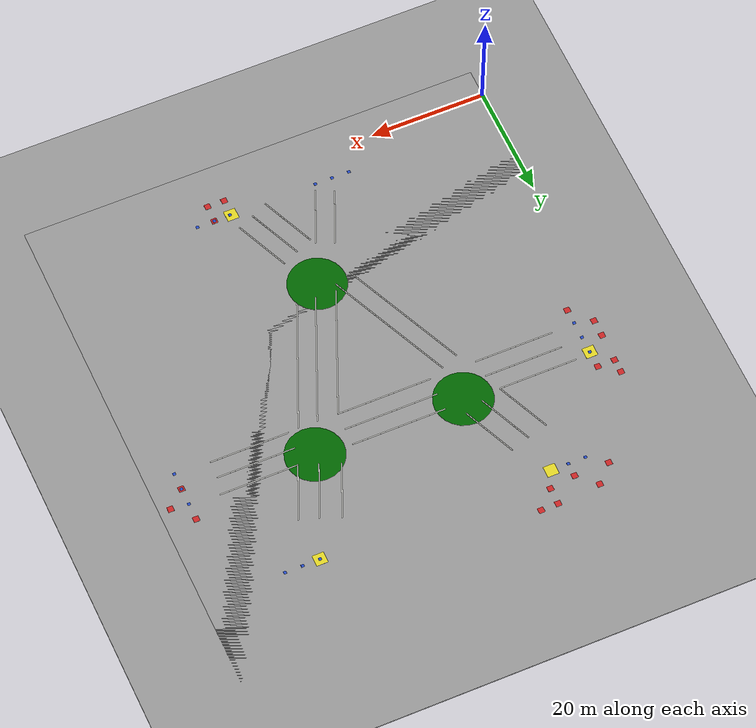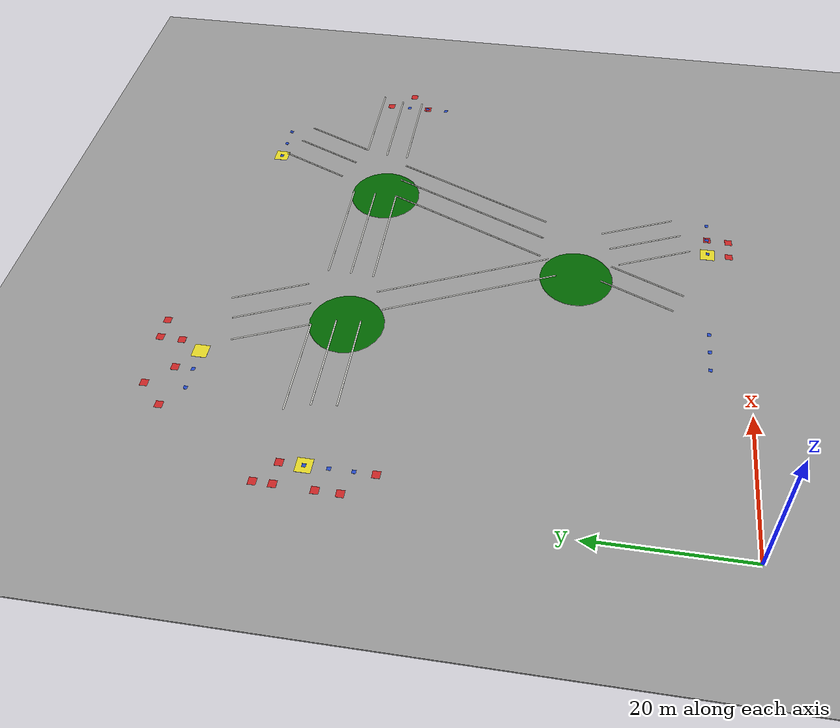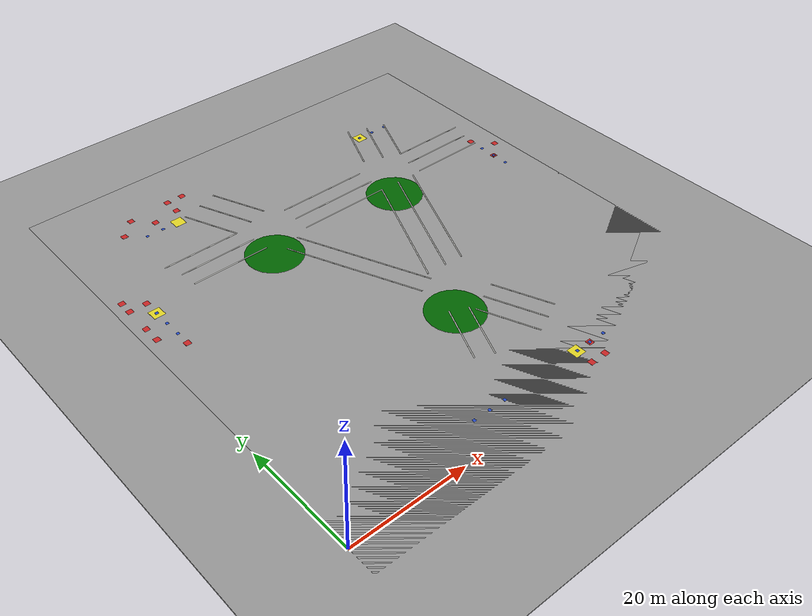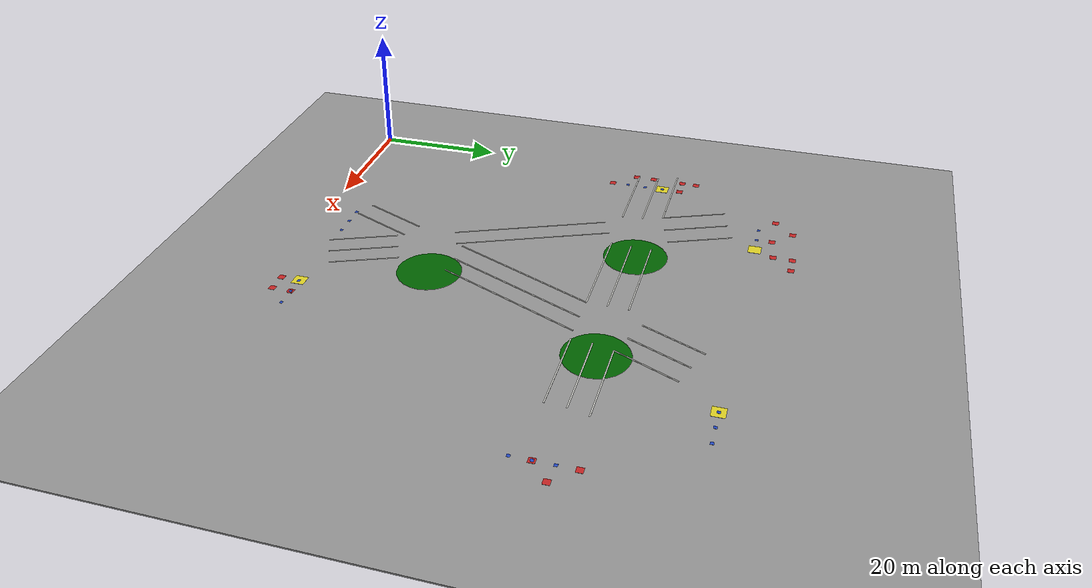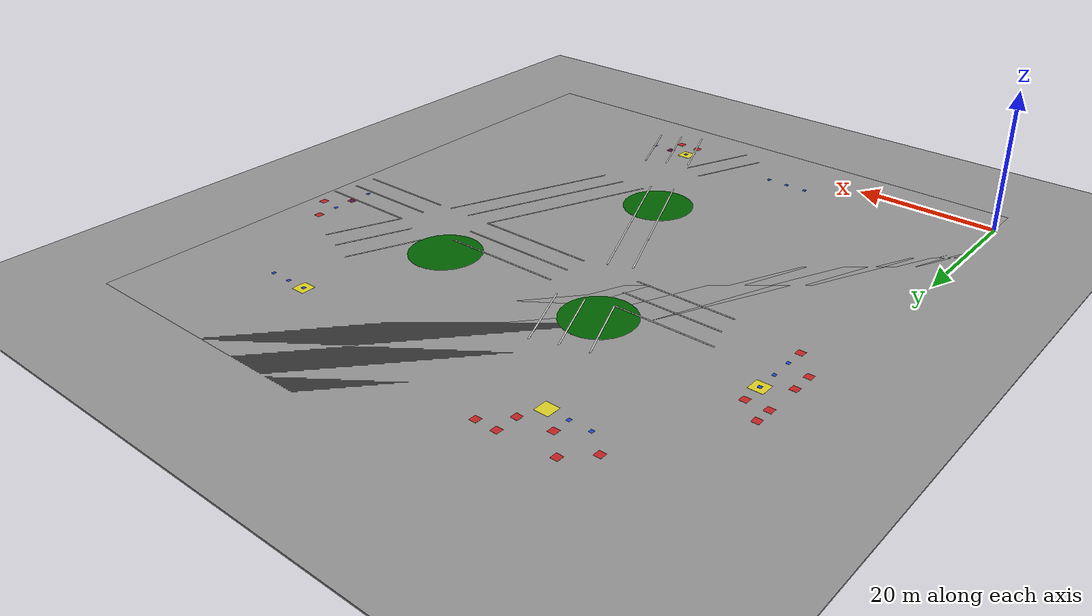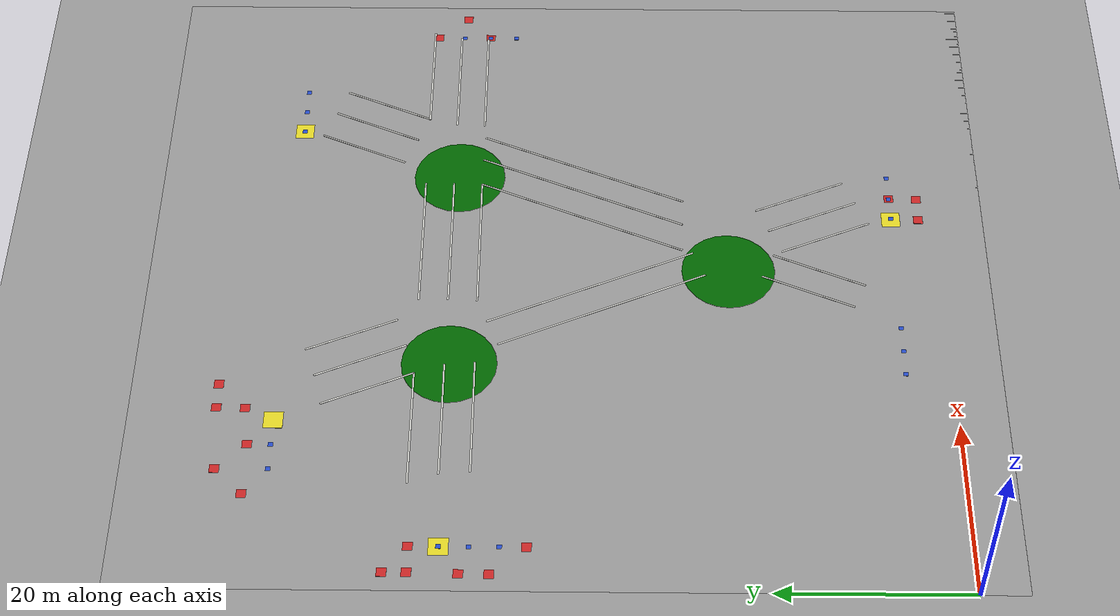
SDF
<sdf version="1.6">
 <world name="default">
  <light name="sun" type="directional">
   <pose>0 0 10 0 -0 0</pose>
   <diffuse>0.8 0.8 0.8 1</diffuse>
   <specular>0.1 0.1 0.1 1</specular>
   <attenuation>
    <range>1000</range>
    <constant>0.9</constant>
    <linear>0.01</linear>
    <quadratic>0.001</quadratic>
   </attenuation>
   <direction>-0.5 0.5 -1</direction>
  </light>
  <model name="ground_plane">
   <static>1</static>
   <link name="link">
    <collision name="collision">
     <geometry><plane><normal>0 0 1</normal><size>100 100</size></plane></geometry>
     <surface><friction><ode><mu>100</mu><mu2>50</mu2></ode></friction></surface>
    </collision>
    <visual name="visual">
     <cast_shadows>0</cast_shadows>
     <geometry><plane><normal>0 0 1</normal><size>100 100</size></plane></geometry>
     <material>
      <script><uri>file://media/materials/scripts/gazebo.material</uri><name>Gazebo/Grey</name></script>
     </material>
    </visual>
   </link>
  </model>
  <gravity>0 0 -9.8</gravity>
  <magnetic_field>6e-06 2.3e-05 -4.2e-05</magnetic_field>
  <atmosphere type="adiabatic"/>
  <physics name="default_physics" default="0" type="ode">
   <max_step_size>0.001</max_step_size>
   <real_time_factor>1</real_time_factor>
   <real_time_update_rate>1000</real_time_update_rate>
  </physics>
  <scene><ambient>0.4 0.4 0.4 1</ambient><background>0.7 0.7 0.7 1</background><shadows>1</shadows></scene>
  <spherical_coordinates>
   <surface_model>EARTH_WGS84</surface_model>
   <latitude_deg>0</latitude_deg>
   <longitude_deg>0</longitude_deg>
   <elevation>0</elevation>
   <heading_deg>0</heading_deg>
  </spherical_coordinates>
  <model name="my_objectT1">
   <link name="my_box">
    <inertial>
     <mass>1</mass>
     <inertia><ixx>1</ixx><ixy>0</ixy><ixz>0</ixz><iyy>100</iyy><iyz>0</iyz><izz>1</izz></inertia>
    </inertial>
    <collision name="my_box_collision"><geometry><box><size>2 2 0.01</size></box></geometry></collision>
    <visual name="my_box_visual">
     <geometry><box><size>2 2 0.01</size></box></geometry>
     <material>
      <script><name>Gazebo/Yellow</name><uri>file://media/materials/scripts/gazebo.material</uri></script>
     </material>
    </visual>
   </link>
   <pose>19.9994 70.0003 0.114978 3e-05 -0 0.000109</pose>
  </model>
  <model name="my_objectT2">
   <link name="my_box">
    <inertial>
     <mass>1</mass>
     <inertia><ixx>1</ixx><ixy>0</ixy><ixz>0</ixz><iyy>100</iyy><iyz>0</iyz><izz>1</izz></inertia>
    </inertial>
    <collision name="my_box_collision"><geometry><box><size>2 2 0.01</size></box></geometry></collision>
    <visual name="my_box_visual">
     <geometry><box><size>2 2 0.01</size></box></geometry>
     <material>
      <script><name>Gazebo/Yellow</name><uri>file://media/materials/scripts/gazebo.material</uri></script>
     </material>
    </visual>
   </link>
   <pose>60.0006 69.9971 0.105 0 -0 2.9e-05</pose>
  </model>
  <model name="my_objectT3">
   <link name="my_box">
    <inertial>
     <mass>1</mass>
     <inertia><ixx>1</ixx><ixy>0</ixy><ixz>0</ixz><iyy>100</iyy><iyz>0</iyz><izz>1</izz></inertia>
    </inertial>
    <collision name="my_box_collision"><geometry><box><size>2 2 0.01</size></box></geometry></collision>
    <visual name="my_box_visual">
     <geometry><box><size>2 2 0.01</size></box></geometry>
     <material>
      <script><name>Gazebo/Yellow</name><uri>file://media/materials/scripts/gazebo.material</uri></script>
     </material>
    </visual>
   </link>
   <pose>5.00081 52.4973 0.104988 3e-06 -0 0.000593</pose>
  </model>
  <model name="my_objectT4">
   <link name="my_box">
    <inertial>
     <mass>1</mass>
     <inertia><ixx>1</ixx><ixy>0</ixy><ixz>0</ixz><iyy>100</iyy><iyz>0</iyz><izz>1</izz></inertia>
    </inertial>
    <collision name="my_box_collision"><geometry><box><size>2 2 0.01</size></box></geometry></collision>
    <visual name="my_box_visual">
     <geometry><box><size>2 2 0.01</size></box></geometry>
     <material>
      <script><name>Gazebo/Yellow</name><uri>file://media/materials/scripts/gazebo.material</uri></script>
     </material>
    </visual>
   </link>
   <pose>47.4911 4.99596 0.114989 5e-06 2.5e-05 0.003713</pose>
  </model>
  <model name="my_objecteg1w1">
   <link name="my_box">
    <inertial>
     <mass>1</mass>
     <inertia><ixx>1</ixx><ixy>0</ixy><ixz>0</ixz><iyy>100</iyy><iyz>0</iyz><izz>1</izz></inertia>
    </inertial>
    <collision name="my_box_collision"><geometry><box><size>1 1 0.01</size></box></geometry></collision>
    <visual name="my_box_visual">
     <geometry><box><size>1 1 0.01</size></box></geometry>
     <material>
      <script><name>Gazebo/Red</name><uri>file://media/materials/scripts/gazebo.material</uri></script>
     </material>
    </visual>
   </link>
   <pose>1.87822 47.4283 0.104995 0 -0 0</pose>
  </model>
  <model name="my_objecteg1w2">
   <link name="my_box">
    <inertial>
     <mass>1</mass>
     <inertia><ixx>1</ixx><ixy>0</ixy><ixz>0</ixz><iyy>100</iyy><iyz>0</iyz><izz>1</izz></inertia>
    </inertial>
    <collision name="my_box_collision"><geometry><box><size>1 1 0.01</size></box></geometry></collision>
    <visual name="my_box_visual">
     <geometry><box><size>1 1 0.01</size></box></geometry>
     <material>
      <script><name>Gazebo/Red</name><uri>file://media/materials/scripts/gazebo.material</uri></script>
     </material>
    </visual>
   </link>
   <pose>5 55.5 0.105 0 -0 0</pose>
  </model>
  <model name="my_objecteg1w3">
   <link name="my_box">
    <inertial>
     <mass>1</mass>
     <inertia><ixx>1</ixx><ixy>0</ixy><ixz>0</ixz><iyy>100</iyy><iyz>0</iyz><izz>1</izz></inertia>
    </inertial>
    <collision name="my_box_collision"><geometry><box><size>1 1 0.01</size></box></geometry></collision>
    <visual name="my_box_visual">
     <geometry><box><size>1 1 0.01</size></box></geometry>
     <material>
      <script><name>Gazebo/Red</name><uri>file://media/materials/scripts/gazebo.material</uri></script>
     </material>
    </visual>
   </link>
   <pose>1.88887 50.4375 0.104991 0 -0 0.000124</pose>
  </model>
  <model name="my_objecteg2w1">
   <link name="my_box">
    <inertial>
     <mass>1</mass>
     <inertia><ixx>1</ixx><ixy>0</ixy><ixz>0</ixz><iyy>100</iyy><iyz>0</iyz><izz>1</izz></inertia>
    </inertial>
    <collision name="my_box_collision"><geometry><box><size>1 1 0.01</size></box></geometry></collision>
    <visual name="my_box_visual">
     <geometry><box><size>1 1 0.01</size></box></geometry>
     <material>
      <script><name>Gazebo/Red</name><uri>file://media/materials/scripts/gazebo.material</uri></script>
     </material>
    </visual>
   </link>
   <pose>78 52.2 0.104991 0 -0 0</pose>
  </model>
  <model name="my_objecteg2w2">
   <link name="my_box">
    <inertial>
     <mass>1</mass>
     <inertia><ixx>1</ixx><ixy>0</ixy><ixz>0</ixz><iyy>100</iyy><iyz>0</iyz><izz>1</izz></inertia>
    </inertial>
    <collision name="my_box_collision"><geometry><box><size>1 1 0.01</size></box></geometry></collision>
    <visual name="my_box_visual">
     <geometry><box><size>1 1 0.01</size></box></geometry>
     <material>
      <script><name>Gazebo/Red</name><uri>file://media/materials/scripts/gazebo.material</uri></script>
     </material>
    </visual>
   </link>
   <pose>75 55.5 0.104998 0 -0 0</pose>
  </model>
  <model name="my_objecteg2w3">
   <link name="my_box">
    <inertial>
     <mass>1</mass>
     <inertia><ixx>1</ixx><ixy>0</ixy><ixz>0</ixz><iyy>100</iyy><iyz>0</iyz><izz>1</izz></inertia>
    </inertial>
    <collision name="my_box_collision"><geometry><box><size>1 1 0.01</size></box></geometry></collision>
    <visual name="my_box_visual">
     <geometry><box><size>1 1 0.01</size></box></geometry>
     <material>
      <script><name>Gazebo/Red</name><uri>file://media/materials/scripts/gazebo.material</uri></script>
     </material>
    </visual>
   </link>
   <pose>75.0015 49.4951 0.104998 -4e-06 0 0.00052</pose>
  </model>
  <model name="my_objecteg3w1">
   <link name="my_box">
    <inertial>
     <mass>1</mass>
     <inertia><ixx>1</ixx><ixy>0</ixy><ixz>0</ixz><iyy>100</iyy><iyz>0</iyz><izz>1</izz></inertia>
    </inertial>
    <collision name="my_box_collision"><geometry><box><size>1 1 0.01</size></box></geometry></collision>
    <visual name="my_box_visual">
     <geometry><box><size>1 1 0.01</size></box></geometry>
     <material>
      <script><name>Gazebo/Red</name><uri>file://media/materials/scripts/gazebo.material</uri></script>
     </material>
    </visual>
   </link>
   <pose>50.4299 1.98378 0.104995 0 -0 0</pose>
  </model>
  <model name="my_objecteg3w2">
   <link name="my_box">
    <inertial>
     <mass>1</mass>
     <inertia><ixx>1</ixx><ixy>0</ixy><ixz>0</ixz><iyy>100</iyy><iyz>0</iyz><izz>1</izz></inertia>
    </inertial>
    <collision name="my_box_collision"><geometry><box><size>1 1 0.01</size></box></geometry></collision>
    <visual name="my_box_visual">
     <geometry><box><size>1 1 0.01</size></box></geometry>
     <material>
      <script><name>Gazebo/Red</name><uri>file://media/materials/scripts/gazebo.material</uri></script>
     </material>
    </visual>
   </link>
   <pose>50.4995 4.99539 0.105002 0 3e-06 0.000328</pose>
  </model>
  <model name="my_objecteg3w3">
   <link name="my_box">
    <inertial>
     <mass>1</mass>
     <inertia><ixx>1</ixx><ixy>0</ixy><ixz>0</ixz><iyy>100</iyy><iyz>0</iyz><izz>1</izz></inertia>
    </inertial>
    <collision name="my_box_collision"><geometry><box><size>1 1 0.01</size></box></geometry></collision>
    <visual name="my_box_visual">
     <geometry><box><size>1 1 0.01</size></box></geometry>
     <material>
      <script><name>Gazebo/Red</name><uri>file://media/materials/scripts/gazebo.material</uri></script>
     </material>
    </visual>
   </link>
   <pose>47.5 2 0.104998 0 -0 0</pose>
  </model>
  <model name="my_objecteg4w1">
   <link name="my_box">
    <inertial>
     <mass>1</mass>
     <inertia><ixx>1</ixx><ixy>0</ixy><ixz>0</ixz><iyy>100</iyy><iyz>0</iyz><izz>1</izz></inertia>
    </inertial>
    <collision name="my_box_collision"><geometry><box><size>1 1 0.01</size></box></geometry></collision>
    <visual name="my_box_visual">
     <geometry><box><size>1 1 0.01</size></box></geometry>
     <material>
      <script><name>Gazebo/Red</name><uri>file://media/materials/scripts/gazebo.material</uri></script>
     </material>
    </visual>
   </link>
   <pose>2.0174 55.4814 0.104998 0 -0 0</pose>
  </model>
  <model name="my_objecteg4w2">
   <link name="my_box">
    <inertial>
     <mass>1</mass>
     <inertia><ixx>1</ixx><ixy>0</ixy><ixz>0</ixz><iyy>100</iyy><iyz>0</iyz><izz>1</izz></inertia>
    </inertial>
    <collision name="my_box_collision"><geometry><box><size>1 1 0.01</size></box></geometry></collision>
    <visual name="my_box_visual">
     <geometry><box><size>1 1 0.01</size></box></geometry>
     <material>
      <script><name>Gazebo/Red</name><uri>file://media/materials/scripts/gazebo.material</uri></script>
     </material>
    </visual>
   </link>
   <pose>4.98488 43.8517 0.104999 0 -0 0</pose>
  </model>
  <model name="my_objecteg4w3">
   <link name="my_box">
    <inertial>
     <mass>1</mass>
     <inertia><ixx>1</ixx><ixy>0</ixy><ixz>0</ixz><iyy>100</iyy><iyz>0</iyz><izz>1</izz></inertia>
    </inertial>
    <collision name="my_box_collision"><geometry><box><size>1 1 0.01</size></box></geometry></collision>
    <visual name="my_box_visual">
     <geometry><box><size>1 1 0.01</size></box></geometry>
     <material>
      <script><name>Gazebo/Red</name><uri>file://media/materials/scripts/gazebo.material</uri></script>
     </material>
    </visual>
   </link>
   <pose>2.02781 57.8944 0.104999 0 -0 6e-06</pose>
  </model>
  <model name="my_objecteg5w1">
   <link name="my_box">
    <inertial>
     <mass>1</mass>
     <inertia><ixx>1</ixx><ixy>0</ixy><ixz>0</ixz><iyy>100</iyy><iyz>0</iyz><izz>1</izz></inertia>
    </inertial>
    <collision name="my_box_collision"><geometry><box><size>1 1 0.01</size></box></geometry></collision>
    <visual name="my_box_visual">
     <geometry><box><size>1 1 0.01</size></box></geometry>
     <material>
      <script><name>Gazebo/Red</name><uri>file://media/materials/scripts/gazebo.material</uri></script>
     </material>
    </visual>
   </link>
   <pose>11 72.4 0.104998 0 -0 0</pose>
  </model>
  <model name="my_objecteg5w2">
   <link name="my_box">
    <inertial>
     <mass>1</mass>
     <inertia><ixx>1</ixx><ixy>0</ixy><ixz>0</ixz><iyy>100</iyy><iyz>0</iyz><izz>1</izz></inertia>
    </inertial>
    <collision name="my_box_collision"><geometry><box><size>1 1 0.01</size></box></geometry></collision>
    <visual name="my_box_visual">
     <geometry><box><size>1 1 0.01</size></box></geometry>
     <material>
      <script><name>Gazebo/Red</name><uri>file://media/materials/scripts/gazebo.material</uri></script>
     </material>
    </visual>
   </link>
   <pose>14 75.4 0.104998 0 -0 0</pose>
  </model>
  <model name="my_objecteg5w3">
   <link name="my_box">
    <inertial>
     <mass>1</mass>
     <inertia><ixx>1</ixx><ixy>0</ixy><ixz>0</ixz><iyy>100</iyy><iyz>0</iyz><izz>1</izz></inertia>
    </inertial>
    <collision name="my_box_collision"><geometry><box><size>1 1 0.01</size></box></geometry></collision>
    <visual name="my_box_visual">
     <geometry><box><size>1 1 0.01</size></box></geometry>
     <material>
      <script><name>Gazebo/Red</name><uri>file://media/materials/scripts/gazebo.material</uri></script>
     </material>
    </visual>
   </link>
   <pose>17 72.4 0.104998 0 -0 0</pose>
  </model>
  <model name="my_objecteg6w1">
   <link name="my_box">
    <inertial>
     <mass>1</mass>
     <inertia><ixx>1</ixx><ixy>0</ixy><ixz>0</ixz><iyy>100</iyy><iyz>0</iyz><izz>1</izz></inertia>
    </inertial>
    <collision name="my_box_collision"><geometry><box><size>1 1 0.01</size></box></geometry></collision>
    <visual name="my_box_visual">
     <geometry><box><size>1 1 0.01</size></box></geometry>
     <material>
      <script><name>Gazebo/Red</name><uri>file://media/materials/scripts/gazebo.material</uri></script>
     </material>
    </visual>
   </link>
   <pose>21.5 73 0.104998 0 -0 0</pose>
  </model>
  <model name="my_objecteg6w2">
   <link name="my_box">
    <inertial>
     <mass>1</mass>
     <inertia><ixx>1</ixx><ixy>0</ixy><ixz>0</ixz><iyy>100</iyy><iyz>0</iyz><izz>1</izz></inertia>
    </inertial>
    <collision name="my_box_collision"><geometry><box><size>1 1 0.01</size></box></geometry></collision>
    <visual name="my_box_visual">
     <geometry><box><size>1 1 0.01</size></box></geometry>
     <material>
      <script><name>Gazebo/Red</name><uri>file://media/materials/scripts/gazebo.material</uri></script>
     </material>
    </visual>
   </link>
   <pose>24.5 76 0.104998 0 -0 0</pose>
  </model>
  <model name="my_objecteg6w3">
   <link name="my_box">
    <inertial>
     <mass>1</mass>
     <inertia><ixx>1</ixx><ixy>0</ixy><ixz>0</ixz><iyy>100</iyy><iyz>0</iyz><izz>1</izz></inertia>
    </inertial>
    <collision name="my_box_collision"><geometry><box><size>1 1 0.01</size></box></geometry></collision>
    <visual name="my_box_visual">
     <geometry><box><size>1 1 0.01</size></box></geometry>
     <material>
      <script><name>Gazebo/Red</name><uri>file://media/materials/scripts/gazebo.material</uri></script>
     </material>
    </visual>
   </link>
   <pose>21.5535 75.9732 0.104991 0 -0 0</pose>
  </model>
  <model name="my_objectg1w1">
   <link name="my_box">
    <inertial>
     <mass>1</mass>
     <inertia><ixx>1</ixx><ixy>0</ixy><ixz>0</ixz><iyy>100</iyy><iyz>0</iyz><izz>1</izz></inertia>
    </inertial>
    <collision name="my_box_collision"><geometry><box><size>0.5 0.5 0.01</size></box></geometry></collision>
    <visual name="my_box_visual">
     <geometry><box><size>0.5 0.5 0.01</size></box></geometry>
     <material>
      <script><name>Gazebo/Blue</name><uri>file://media/materials/scripts/gazebo.material</uri></script>
     </material>
    </visual>
   </link>
   <pose>47.4983 5.0049 0.105007 8e-06 1.9e-05 -0.001771</pose>
  </model>
  <model name="my_objectg1w2">
   <link name="my_box">
    <inertial>
     <mass>1</mass>
     <inertia><ixx>1</ixx><ixy>0</ixy><ixz>0</ixz><iyy>100</iyy><iyz>0</iyz><izz>1</izz></inertia>
    </inertial>
    <collision name="my_box_collision"><geometry><box><size>0.5 0.5 0.01</size></box></geometry></collision>
    <visual name="my_box_visual">
     <geometry><box><size>0.5 0.5 0.01</size></box></geometry>
     <material>
      <script><name>Gazebo/Blue</name><uri>file://media/materials/scripts/gazebo.material</uri></script>
     </material>
    </visual>
   </link>
   <pose>50.497 5.00193 0.115024 8.8e-05 3e-06 0.000456</pose>
  </model>
  <model name="my_objectg1w3">
   <link name="my_box">
    <inertial>
     <mass>1</mass>
     <inertia><ixx>1</ixx><ixy>0</ixy><ixz>0</ixz><iyy>100</iyy><iyz>0</iyz><izz>1</izz></inertia>
    </inertial>
    <collision name="my_box_collision"><geometry><box><size>0.5 0.5 0.01</size></box></geometry></collision>
    <visual name="my_box_visual">
     <geometry><box><size>0.5 0.5 0.01</size></box></geometry>
     <material>
      <script><name>Gazebo/Blue</name><uri>file://media/materials/scripts/gazebo.material</uri></script>
     </material>
    </visual>
   </link>
   <pose>53.4967 5.0058 0.104999 -5e-06 -1e-06 -0.000646</pose>
  </model>
  <model name="my_objectg2w1">
   <link name="my_box">
    <inertial>
     <mass>1</mass>
     <inertia><ixx>1</ixx><ixy>0</ixy><ixz>0</ixz><iyy>100</iyy><iyz>0</iyz><izz>1</izz></inertia>
    </inertial>
    <collision name="my_box_collision"><geometry><box><size>0.5 0.5 0.01</size></box></geometry></collision>
    <visual name="my_box_visual">
     <geometry><box><size>0.5 0.5 0.01</size></box></geometry>
     <material>
      <script><name>Gazebo/Blue</name><uri>file://media/materials/scripts/gazebo.material</uri></script>
     </material>
    </visual>
   </link>
   <pose>32.4963 5.0067 0.105 0 0 -0.000415</pose>
  </model>
  <model name="my_objectg2w2">
   <link name="my_box">
    <inertial>
     <mass>1</mass>
     <inertia><ixx>1</ixx><ixy>0</ixy><ixz>0</ixz><iyy>100</iyy><iyz>0</iyz><izz>1</izz></inertia>
    </inertial>
    <collision name="my_box_collision"><geometry><box><size>0.5 0.5 0.01</size></box></geometry></collision>
    <visual name="my_box_visual">
     <geometry><box><size>0.5 0.5 0.01</size></box></geometry>
     <material>
      <script><name>Gazebo/Blue</name><uri>file://media/materials/scripts/gazebo.material</uri></script>
     </material>
    </visual>
   </link>
   <pose>29.4959 5.0064 0.105 -0 2e-06 -0.000442</pose>
  </model>
  <model name="my_objectg2w3">
   <link name="my_box">
    <inertial>
     <mass>1</mass>
     <inertia><ixx>1</ixx><ixy>0</ixy><ixz>0</ixz><iyy>100</iyy><iyz>0</iyz><izz>1</izz></inertia>
    </inertial>
    <collision name="my_box_collision"><geometry><box><size>0.5 0.5 0.01</size></box></geometry></collision>
    <visual name="my_box_visual">
     <geometry><box><size>0.5 0.5 0.01</size></box></geometry>
     <material>
      <script><name>Gazebo/Blue</name><uri>file://media/materials/scripts/gazebo.material</uri></script>
     </material>
    </visual>
   </link>
   <pose>26.4956 5.00747 0.105001 1e-06 1e-06 -0.00119</pose>
  </model>
  <model name="my_objectg3w1">
   <link name="my_box">
    <inertial>
     <mass>1</mass>
     <inertia><ixx>1</ixx><ixy>0</ixy><ixz>0</ixz><iyy>100</iyy><iyz>0</iyz><izz>1</izz></inertia>
    </inertial>
    <collision name="my_box_collision"><geometry><box><size>0.5 0.5 0.01</size></box></geometry></collision>
    <visual name="my_box_visual">
     <geometry><box><size>0.5 0.5 0.01</size></box></geometry>
     <material>
      <script><name>Gazebo/Blue</name><uri>file://media/materials/scripts/gazebo.material</uri></script>
     </material>
    </visual>
   </link>
   <pose>19.9965 70.0042 0.105 1e-06 0 -2e-06</pose>
  </model>
  <model name="my_objectg3w2">
   <link name="my_box">
    <inertial>
     <mass>1</mass>
     <inertia><ixx>1</ixx><ixy>0</ixy><ixz>0</ixz><iyy>100</iyy><iyz>0</iyz><izz>1</izz></inertia>
    </inertial>
    <collision name="my_box_collision"><geometry><box><size>0.5 0.5 0.01</size></box></geometry></collision>
    <visual name="my_box_visual">
     <geometry><box><size>0.5 0.5 0.01</size></box></geometry>
     <material>
      <script><name>Gazebo/Blue</name><uri>file://media/materials/scripts/gazebo.material</uri></script>
     </material>
    </visual>
   </link>
   <pose>16.9945 70.0086 0.104999 -5e-06 1e-06 -0.000992</pose>
  </model>
  <model name="my_objectg3w3">
   <link name="my_box">
    <inertial>
     <mass>1</mass>
     <inertia><ixx>1</ixx><ixy>0</ixy><ixz>0</ixz><iyy>100</iyy><iyz>0</iyz><izz>1</izz></inertia>
    </inertial>
    <collision name="my_box_collision"><geometry><box><size>0.5 0.5 0.01</size></box></geometry></collision>
    <visual name="my_box_visual">
     <geometry><box><size>0.5 0.5 0.01</size></box></geometry>
     <material>
      <script><name>Gazebo/Blue</name><uri>file://media/materials/scripts/gazebo.material</uri></script>
     </material>
    </visual>
   </link>
   <pose>13.9943 70.0089 0.105001 3e-06 1e-06 0.000768</pose>
  </model>
  <model name="my_objectg4w1">
   <link name="my_box">
    <inertial>
     <mass>1</mass>
     <inertia><ixx>1</ixx><ixy>0</ixy><ixz>0</ixz><iyy>100</iyy><iyz>0</iyz><izz>1</izz></inertia>
    </inertial>
    <collision name="my_box_collision"><geometry><box><size>0.5 0.5 0.01</size></box></geometry></collision>
    <visual name="my_box_visual">
     <geometry><box><size>0.5 0.5 0.01</size></box></geometry>
     <material>
      <script><name>Gazebo/Blue</name><uri>file://media/materials/scripts/gazebo.material</uri></script>
     </material>
    </visual>
   </link>
   <pose>4.99434 52.5091 0.114994 -1.7e-05 3e-06 0.000934</pose>
  </model>
  <model name="my_objectg4w2">
   <link name="my_box">
    <inertial>
     <mass>1</mass>
     <inertia><ixx>1</ixx><ixy>0</ixy><ixz>0</ixz><iyy>100</iyy><iyz>0</iyz><izz>1</izz></inertia>
    </inertial>
    <collision name="my_box_collision"><geometry><box><size>0.5 0.5 0.01</size></box></geometry></collision>
    <visual name="my_box_visual">
     <geometry><box><size>0.5 0.5 0.01</size></box></geometry>
     <material>
      <script><name>Gazebo/Blue</name><uri>file://media/materials/scripts/gazebo.material</uri></script>
     </material>
    </visual>
   </link>
   <pose>4.99224 49.5116 0.104975 -2e-06 1e-06 -0.00042</pose>
  </model>
  <model name="my_objectg4w3">
   <link name="my_box">
    <inertial>
     <mass>1</mass>
     <inertia><ixx>1</ixx><ixy>0</ixy><ixz>0</ixz><iyy>100</iyy><iyz>0</iyz><izz>1</izz></inertia>
    </inertial>
    <collision name="my_box_collision"><geometry><box><size>0.5 0.5 0.01</size></box></geometry></collision>
    <visual name="my_box_visual">
     <geometry><box><size>0.5 0.5 0.01</size></box></geometry>
     <material>
      <script><name>Gazebo/Blue</name><uri>file://media/materials/scripts/gazebo.material</uri></script>
     </material>
    </visual>
   </link>
   <pose>4.99295 46.5109 0.105002 -1e-06 -8e-06 -0.000557</pose>
  </model>
  <model name="my_objectg5w1">
   <link name="my_box">
    <inertial>
     <mass>1</mass>
     <inertia><ixx>1</ixx><ixy>0</ixy><ixz>0</ixz><iyy>100</iyy><iyz>0</iyz><izz>1</izz></inertia>
    </inertial>
    <collision name="my_box_collision"><geometry><box><size>0.5 0.5 0.01</size></box></geometry></collision>
    <visual name="my_box_visual">
     <geometry><box><size>0.5 0.5 0.01</size></box></geometry>
     <material>
      <script><name>Gazebo/Blue</name><uri>file://media/materials/scripts/gazebo.material</uri></script>
     </material>
    </visual>
   </link>
   <pose>74.992 52.5122 0.105001 3e-06 1e-06 -0.000576</pose>
  </model>
  <model name="my_objectg5w2">
   <link name="my_box">
    <inertial>
     <mass>1</mass>
     <inertia><ixx>1</ixx><ixy>0</ixy><ixz>0</ixz><iyy>100</iyy><iyz>0</iyz><izz>1</izz></inertia>
    </inertial>
    <collision name="my_box_collision"><geometry><box><size>0.5 0.5 0.01</size></box></geometry></collision>
    <visual name="my_box_visual">
     <geometry><box><size>0.5 0.5 0.01</size></box></geometry>
     <material>
      <script><name>Gazebo/Blue</name><uri>file://media/materials/scripts/gazebo.material</uri></script>
     </material>
    </visual>
   </link>
   <pose>74.9924 49.5074 0.11502 -8.6e-05 -7e-06 -0.001803</pose>
  </model>
  <model name="my_objectg5w3">
   <link name="my_box">
    <inertial>
     <mass>1</mass>
     <inertia><ixx>1</ixx><ixy>0</ixy><ixz>0</ixz><iyy>100</iyy><iyz>0</iyz><izz>1</izz></inertia>
    </inertial>
    <collision name="my_box_collision"><geometry><box><size>0.5 0.5 0.01</size></box></geometry></collision>
    <visual name="my_box_visual">
     <geometry><box><size>0.5 0.5 0.01</size></box></geometry>
     <material>
      <script><name>Gazebo/Blue</name><uri>file://media/materials/scripts/gazebo.material</uri></script>
     </material>
    </visual>
   </link>
   <pose>74.993 46.5121 0.104966 1e-06 0 -0.000571</pose>
  </model>
  <model name="my_objectg6w1">
   <link name="my_box">
    <inertial>
     <mass>1</mass>
     <inertia><ixx>1</ixx><ixy>0</ixy><ixz>0</ixz><iyy>100</iyy><iyz>0</iyz><izz>1</izz></inertia>
    </inertial>
    <collision name="my_box_collision"><geometry><box><size>0.5 0.5 0.01</size></box></geometry></collision>
    <visual name="my_box_visual">
     <geometry><box><size>0.5 0.5 0.01</size></box></geometry>
     <material>
      <script><name>Gazebo/Blue</name><uri>file://media/materials/scripts/gazebo.material</uri></script>
     </material>
    </visual>
   </link>
   <pose>59.9923 70.0121 0.115001 0 -2e-06 -0.002283</pose>
  </model>
  <model name="my_objectg6w2">
   <link name="my_box">
    <inertial>
     <mass>1</mass>
     <inertia><ixx>1</ixx><ixy>0</ixy><ixz>0</ixz><iyy>100</iyy><iyz>0</iyz><izz>1</izz></inertia>
    </inertial>
    <collision name="my_box_collision"><geometry><box><size>0.5 0.5 0.01</size></box></geometry></collision>
    <visual name="my_box_visual">
     <geometry><box><size>0.5 0.5 0.01</size></box></geometry>
     <material>
      <script><name>Gazebo/Blue</name><uri>file://media/materials/scripts/gazebo.material</uri></script>
     </material>
    </visual>
   </link>
   <pose>62.9903 70.0147 0.105004 0 -1.5e-05 -0.000336</pose>
  </model>
  <model name="my_objectg6w3">
   <link name="my_box">
    <inertial>
     <mass>1</mass>
     <inertia><ixx>1</ixx><ixy>0</ixy><ixz>0</ixz><iyy>100</iyy><iyz>0</iyz><izz>1</izz></inertia>
    </inertial>
    <collision name="my_box_collision"><geometry><box><size>0.5 0.5 0.01</size></box></geometry></collision>
    <visual name="my_box_visual">
     <geometry><box><size>0.5 0.5 0.01</size></box></geometry>
     <material>
      <script><name>Gazebo/Blue</name><uri>file://media/materials/scripts/gazebo.material</uri></script>
     </material>
    </visual>
   </link>
   <pose>65.9897 70.0155 0.104996 1.9e-05 2e-06 -0.000672</pose>
  </model>
  <model name="35_clone_1">
   <link name="Wall_2">
    <pose>0 0 0 0 -0 1.9706</pose>
    <gravity>0</gravity>
    <inertial>
     <mass>1</mass>
     <inertia><ixx>1</ixx><ixy>0</ixy><ixz>0</ixz><iyy>1</iyy><iyz>0</iyz><izz>1</izz></inertia>
    </inertial>
    <visual name="Wall_2_Visual">
     <pose>0 0 5 0 -0 0</pose>
     <geometry><box><size>10.2688 0.2 0.01</size></box></geometry>
     <material>
      <script><uri>file://media/materials/scripts/gazebo.material</uri><name>Gazebo/CeilingTiled</name></script>
      <ambient>0.435 0.796 0.675 1</ambient>
      <diffuse>1 1 1 1</diffuse>
      <specular>0 0 0 1</specular>
      <emissive>1 1 0 0</emissive>
      <shader type="vertex"><normal_map>__default__</normal_map></shader>
     </material>
    </visual>
    <collision name="Wall_2_Collision">
     <pose>0 0 1.25 0 -0 0</pose>
     <geometry><box><size>10.2688 0.001 2.5</size></box></geometry>
     <surface>
      <friction>
       <ode><mu>1</mu><mu2>1</mu2><fdir1>0 0 0</fdir1><slip1>0</slip1><slip2>0</slip2></ode>
       <torsional>
        <coefficient>1</coefficient>
        <patch_radius>0</patch_radius>
        <surface_radius>0</surface_radius>
        <use_patch_radius>1</use_patch_radius>
        <ode><slip>0</slip></ode>
       </torsional>
      </friction>
      <bounce><restitution_coefficient>0</restitution_coefficient><threshold>1e+06</threshold></bounce>
      <contact>
       <collide_without_contact>0</collide_without_contact>
       <collide_without_contact_bitmask>1</collide_without_contact_bitmask>
       <collide_bitmask>1</collide_bitmask>
       <ode>
        <soft_cfm>0</soft_cfm>
        <soft_erp>0.2</soft_erp>
        <kp>1e+13</kp>
        <kd>1</kd>
        <max_vel>0.01</max_vel>
        <min_depth>0</min_depth>
       </ode>
       <bullet>
        <split_impulse>1</split_impulse>
        <split_impulse_penetration_threshold>-0.01</split_impulse_penetration_threshold>
        <soft_cfm>0</soft_cfm>
        <soft_erp>0.2</soft_erp>
        <kp>1e+13</kp>
        <kd>1</kd>
       </bullet>
      </contact>
     </surface>
    </collision>
   </link>
   <static>1</static>
   <pose>40.7717 12.9054 0 0 -0 0</pose>
  </model>
  <model name="35_clone_0_0">
   <link name="Wall_2">
    <pose>0 0 0 0 -0 1.9706</pose>
    <gravity>0</gravity>
    <inertial>
     <mass>1</mass>
     <inertia><ixx>1</ixx><ixy>0</ixy><ixz>0</ixz><iyy>1</iyy><iyz>0</iyz><izz>1</izz></inertia>
    </inertial>
    <visual name="Wall_2_Visual">
     <pose>0 0 5 0 -0 0</pose>
     <geometry><box><size>10.2688 0.2 0.01</size></box></geometry>
     <material>
      <script><uri>file://media/materials/scripts/gazebo.material</uri><name>Gazebo/CeilingTiled</name></script>
      <ambient>0.435 0.796 0.675 1</ambient>
      <diffuse>1 1 1 1</diffuse>
      <specular>0 0 0 1</specular>
      <emissive>1 1 0 1</emissive>
      <shader type="vertex"><normal_map>__default__</normal_map></shader>
     </material>
    </visual>
    <collision name="Wall_2_Collision">
     <pose>0 0 1.25 0 -0 0</pose>
     <geometry><box><size>10.2688 0.001 2.5</size></box></geometry>
     <surface>
      <friction>
       <ode><mu>1</mu><mu2>1</mu2><fdir1>0 0 0</fdir1><slip1>0</slip1><slip2>0</slip2></ode>
       <torsional>
        <coefficient>1</coefficient>
        <patch_radius>0</patch_radius>
        <surface_radius>0</surface_radius>
        <use_patch_radius>1</use_patch_radius>
        <ode><slip>0</slip></ode>
       </torsional>
      </friction>
      <bounce><restitution_coefficient>0</restitution_coefficient><threshold>1e+06</threshold></bounce>
      <contact>
       <collide_without_contact>0</collide_without_contact>
       <collide_without_contact_bitmask>1</collide_without_contact_bitmask>
       <collide_bitmask>1</collide_bitmask>
       <ode>
        <soft_cfm>0</soft_cfm>
        <soft_erp>0.2</soft_erp>
        <kp>1e+13</kp>
        <kd>1</kd>
        <max_vel>0.01</max_vel>
        <min_depth>0</min_depth>
       </ode>
       <bullet>
        <split_impulse>1</split_impulse>
        <split_impulse_penetration_threshold>-0.01</split_impulse_penetration_threshold>
        <soft_cfm>0</soft_cfm>
        <soft_erp>0.2</soft_erp>
        <kp>1e+13</kp>
        <kd>1</kd>
       </bullet>
      </contact>
     </surface>
    </collision>
   </link>
   <static>1</static>
   <pose>46.4308 15.422 0 0 -0 0</pose>
  </model>
  <model name="355_clone_0">
   <link name="Wall_12">
    <pose>0 0 0 0 -0 1.17099</pose>
    <gravity>0</gravity>
    <inertial>
     <mass>1</mass>
     <inertia><ixx>1</ixx><ixy>0</ixy><ixz>0</ixz><iyy>1</iyy><iyz>0</iyz><izz>1</izz></inertia>
    </inertial>
    <visual name="Wall_12_Visual">
     <pose>0 0 5 0 -0 0</pose>
     <geometry><box><size>10.2688 0.2 0.01</size></box></geometry>
     <material>
      <script><uri>file://media/materials/scripts/gazebo.material</uri><name>Gazebo/CeilingTiled</name></script>
      <ambient>0.435 0.796 0.675 1</ambient>
      <diffuse>1 1 1 1</diffuse>
      <specular>0 0 0 1</specular>
      <emissive>1 1 0 1</emissive>
      <shader type="vertex"><normal_map>__default__</normal_map></shader>
     </material>
    </visual>
    <collision name="Wall_12_Collision">
     <pose>0 0 1.25 0 -0 0</pose>
     <geometry><box><size>10.2688 0.001 2.5</size></box></geometry>
     <surface>
      <friction>
       <ode><mu>1</mu><mu2>1</mu2><fdir1>0 0 0</fdir1><slip1>0</slip1><slip2>0</slip2></ode>
       <torsional>
        <coefficient>1</coefficient>
        <patch_radius>0</patch_radius>
        <surface_radius>0</surface_radius>
        <use_patch_radius>1</use_patch_radius>
        <ode><slip>0</slip></ode>
       </torsional>
      </friction>
      <bounce><restitution_coefficient>0</restitution_coefficient><threshold>1e+06</threshold></bounce>
      <contact>
       <collide_without_contact>0</collide_without_contact>
       <collide_without_contact_bitmask>1</collide_without_contact_bitmask>
       <collide_bitmask>1</collide_bitmask>
       <ode>
        <soft_cfm>0</soft_cfm>
        <soft_erp>0.2</soft_erp>
        <kp>1e+13</kp>
        <kd>1</kd>
        <max_vel>0.01</max_vel>
        <min_depth>0</min_depth>
       </ode>
       <bullet>
        <split_impulse>1</split_impulse>
        <split_impulse_penetration_threshold>-0.01</split_impulse_penetration_threshold>
        <soft_cfm>0</soft_cfm>
        <soft_erp>0.2</soft_erp>
        <kp>1e+13</kp>
        <kd>1</kd>
       </bullet>
      </contact>
     </surface>
    </collision>
   </link>
   <static>1</static>
   <pose>36.2739 13.8279 0 0 -0 0</pose>
  </model>
  <model name="355_0">
   <link name="Wall_12">
    <pose>0 0 0 0 -0 1.17099</pose>
    <gravity>0</gravity>
    <inertial>
     <mass>1</mass>
     <inertia><ixx>1</ixx><ixy>0</ixy><ixz>0</ixz><iyy>1</iyy><iyz>0</iyz><izz>1</izz></inertia>
    </inertial>
    <visual name="Wall_12_Visual">
     <pose>0 0 5 0 -0 0</pose>
     <geometry><box><size>10.2688 0.2 0.01</size></box></geometry>
     <material>
      <script><uri>file://media/materials/scripts/gazebo.material</uri><name>Gazebo/CeilingTiled</name></script>
      <ambient>0.435 0.796 0.675 1</ambient>
      <diffuse>1 1 1 1</diffuse>
      <specular>0 0 0 1</specular>
      <emissive>1 1 0 1</emissive>
      <shader type="vertex"><normal_map>__default__</normal_map></shader>
     </material>
    </visual>
    <collision name="Wall_12_Collision">
     <pose>0 0 1.25 0 -0 0</pose>
     <geometry><box><size>10.2688 0.001 2.5</size></box></geometry>
     <surface>
      <friction>
       <ode><mu>1</mu><mu2>1</mu2><fdir1>0 0 0</fdir1><slip1>0</slip1><slip2>0</slip2></ode>
       <torsional>
        <coefficient>1</coefficient>
        <patch_radius>0</patch_radius>
        <surface_radius>0</surface_radius>
        <use_patch_radius>1</use_patch_radius>
        <ode><slip>0</slip></ode>
       </torsional>
      </friction>
      <bounce><restitution_coefficient>0</restitution_coefficient><threshold>1e+06</threshold></bounce>
      <contact>
       <collide_without_contact>0</collide_without_contact>
       <collide_without_contact_bitmask>1</collide_without_contact_bitmask>
       <collide_bitmask>1</collide_bitmask>
       <ode>
        <soft_cfm>0</soft_cfm>
        <soft_erp>0.2</soft_erp>
        <kp>1e+13</kp>
        <kd>1</kd>
        <max_vel>0.01</max_vel>
        <min_depth>0</min_depth>
       </ode>
       <bullet>
        <split_impulse>1</split_impulse>
        <split_impulse_penetration_threshold>-0.01</split_impulse_penetration_threshold>
        <soft_cfm>0</soft_cfm>
        <soft_erp>0.2</soft_erp>
        <kp>1e+13</kp>
        <kd>1</kd>
       </bullet>
      </contact>
     </surface>
    </collision>
   </link>
   <static>1</static>
   <pose>33.4162 15.1125 0 0 -0 0</pose>
  </model>
  <model name="351_0_0">
   <link name="Wall_4">
    <pose>0 0 0 0 -0 1.9806</pose>
    <gravity>0</gravity>
    <inertial>
     <mass>1</mass>
     <inertia><ixx>1</ixx><ixy>0</ixy><ixz>0</ixz><iyy>1</iyy><iyz>0</iyz><izz>1</izz></inertia>
    </inertial>
    <visual name="Wall_4_Visual">
     <pose>0 0 5 0 -0 0</pose>
     <geometry><box><size>23.3941 0.2 0.01</size></box></geometry>
     <material>
      <script><uri>file://media/materials/scripts/gazebo.material</uri><name>Gazebo/CeilingTiled</name></script>
      <ambient>0.435 0.796 0.675 1</ambient>
      <diffuse>1 1 1 1</diffuse>
      <specular>0 0 0 1</specular>
      <emissive>1 1 0 1</emissive>
      <shader type="vertex"><normal_map>__default__</normal_map></shader>
     </material>
    </visual>
    <collision name="Wall_4_Collision">
     <pose>0 0 1.25 0 -0 0</pose>
     <geometry><box><size>23.3941 0.001 2.5</size></box></geometry>
     <surface>
      <friction>
       <ode><mu>1</mu><mu2>1</mu2><fdir1>0 0 0</fdir1><slip1>0</slip1><slip2>0</slip2></ode>
       <torsional>
        <coefficient>1</coefficient>
        <patch_radius>0</patch_radius>
        <surface_radius>0</surface_radius>
        <use_patch_radius>1</use_patch_radius>
        <ode><slip>0</slip></ode>
       </torsional>
      </friction>
      <bounce><restitution_coefficient>0</restitution_coefficient><threshold>1e+06</threshold></bounce>
      <contact>
       <collide_without_contact>0</collide_without_contact>
       <collide_without_contact_bitmask>1</collide_without_contact_bitmask>
       <collide_bitmask>1</collide_bitmask>
       <ode>
        <soft_cfm>0</soft_cfm>
        <soft_erp>0.2</soft_erp>
        <kp>1e+13</kp>
        <kd>1</kd>
        <max_vel>0.01</max_vel>
        <min_depth>0</min_depth>
       </ode>
       <bullet>
        <split_impulse>1</split_impulse>
        <split_impulse_penetration_threshold>-0.01</split_impulse_penetration_threshold>
        <soft_cfm>0</soft_cfm>
        <soft_erp>0.2</soft_erp>
        <kp>1e+13</kp>
        <kd>1</kd>
       </bullet>
      </contact>
     </surface>
    </collision>
   </link>
   <static>1</static>
   <pose>33.818 37.6954 0 0 -0 0</pose>
  </model>
  <model name="351_0_clone_0">
   <link name="Wall_4">
    <pose>2e-06 -0 0 0 -0 1.9806</pose>
    <gravity>0</gravity>
    <inertial>
     <mass>1</mass>
     <inertia><ixx>1</ixx><ixy>0</ixy><ixz>0</ixz><iyy>1</iyy><iyz>0</iyz><izz>1</izz></inertia>
    </inertial>
    <visual name="Wall_4_Visual">
     <pose>0 0 5 0 -0 0</pose>
     <geometry><box><size>23.3941 0.2 0.01</size></box></geometry>
     <material>
      <script><uri>file://media/materials/scripts/gazebo.material</uri><name>Gazebo/CeilingTiled</name></script>
      <ambient>0.435 0.796 0.675 1</ambient>
      <diffuse>1 1 1 1</diffuse>
      <specular>0 0 0 1</specular>
      <emissive>1 1 0 1</emissive>
      <shader type="vertex"><normal_map>__default__</normal_map></shader>
     </material>
    </visual>
    <collision name="Wall_4_Collision">
     <pose>0 0 1.25 0 -0 0</pose>
     <geometry><box><size>23.3941 0.001 2.5</size></box></geometry>
     <surface>
      <friction>
       <ode><mu>1</mu><mu2>1</mu2><fdir1>0 0 0</fdir1><slip1>0</slip1><slip2>0</slip2></ode>
       <torsional>
        <coefficient>1</coefficient>
        <patch_radius>0</patch_radius>
        <surface_radius>0</surface_radius>
        <use_patch_radius>1</use_patch_radius>
        <ode><slip>0</slip></ode>
       </torsional>
      </friction>
      <bounce><restitution_coefficient>0</restitution_coefficient><threshold>1e+06</threshold></bounce>
      <contact>
       <collide_without_contact>0</collide_without_contact>
       <collide_without_contact_bitmask>1</collide_without_contact_bitmask>
       <collide_bitmask>1</collide_bitmask>
       <ode>
        <soft_cfm>0</soft_cfm>
        <soft_erp>0.2</soft_erp>
        <kp>1e+13</kp>
        <kd>1</kd>
        <max_vel>0.01</max_vel>
        <min_depth>0</min_depth>
       </ode>
       <bullet>
        <split_impulse>1</split_impulse>
        <split_impulse_penetration_threshold>-0.01</split_impulse_penetration_threshold>
        <soft_cfm>0</soft_cfm>
        <soft_erp>0.2</soft_erp>
        <kp>1e+13</kp>
        <kd>1</kd>
       </bullet>
      </contact>
     </surface>
    </collision>
   </link>
   <static>1</static>
   <pose>30.8667 36.459 0 0 -0 0</pose>
  </model>
  <model name="356_0">
   <link name="Wall_14">
    <pose>0 0 0 0 -0 1.17162</pose>
    <gravity>0</gravity>
    <inertial>
     <mass>1</mass>
     <inertia><ixx>1</ixx><ixy>0</ixy><ixz>0</ixz><iyy>1</iyy><iyz>0</iyz><izz>1</izz></inertia>
    </inertial>
    <visual name="Wall_14_Visual">
     <pose>0 0 5 0 -0 0</pose>
     <geometry><box><size>23.2878 0.2 0.01</size></box></geometry>
     <material>
      <script><uri>file://media/materials/scripts/gazebo.material</uri><name>Gazebo/CeilingTiled</name></script>
      <ambient>0.435 0.796 0.675 1</ambient>
      <diffuse>1 1 1 1</diffuse>
      <specular>0 0 0 1</specular>
      <emissive>1 1 0 1</emissive>
      <shader type="vertex"><normal_map>__default__</normal_map></shader>
     </material>
    </visual>
    <collision name="Wall_14_Collision">
     <pose>0 0 1.25 0 -0 0</pose>
     <geometry><box><size>23.2878 0.001 2.5</size></box></geometry>
     <surface>
      <friction>
       <ode><mu>1</mu><mu2>1</mu2><fdir1>0 0 0</fdir1><slip1>0</slip1><slip2>0</slip2></ode>
       <torsional>
        <coefficient>1</coefficient>
        <patch_radius>0</patch_radius>
        <surface_radius>0</surface_radius>
        <use_patch_radius>1</use_patch_radius>
        <ode><slip>0</slip></ode>
       </torsional>
      </friction>
      <bounce><restitution_coefficient>0</restitution_coefficient><threshold>1e+06</threshold></bounce>
      <contact>
       <collide_without_contact>0</collide_without_contact>
       <collide_without_contact_bitmask>1</collide_without_contact_bitmask>
       <collide_bitmask>1</collide_bitmask>
       <ode>
        <soft_cfm>0</soft_cfm>
        <soft_erp>0.2</soft_erp>
        <kp>1e+13</kp>
        <kd>1</kd>
        <max_vel>0.01</max_vel>
        <min_depth>0</min_depth>
       </ode>
       <bullet>
        <split_impulse>1</split_impulse>
        <split_impulse_penetration_threshold>-0.01</split_impulse_penetration_threshold>
        <soft_cfm>0</soft_cfm>
        <soft_erp>0.2</soft_erp>
        <kp>1e+13</kp>
        <kd>1</kd>
       </bullet>
      </contact>
     </surface>
    </collision>
   </link>
   <static>1</static>
   <pose>43.4074 38.791 0 0 -0 0</pose>
  </model>
  <model name="359_0">
   <link name="Wall_20">
    <gravity>0</gravity>
    <inertial>
     <mass>1</mass>
     <inertia><ixx>1</ixx><ixy>0</ixy><ixz>0</ixz><iyy>1</iyy><iyz>0</iyz><izz>1</izz></inertia>
    </inertial>
    <visual name="Wall_20_Visual">
     <pose>0 0 5 0 -0 0</pose>
     <geometry><box><size>16.1 0.2 0.01</size></box></geometry>
     <material>
      <script><uri>file://media/materials/scripts/gazebo.material</uri><name>Gazebo/CeilingTiled</name></script>
      <ambient>0.435 0.796 0.675 1</ambient>
      <diffuse>1 1 1 1</diffuse>
      <specular>0 0 0 1</specular>
      <emissive>1 1 0 1</emissive>
      <shader type="vertex"><normal_map>__default__</normal_map></shader>
     </material>
    </visual>
    <collision name="Wall_20_Collision">
     <pose>0 0 1.25 0 -0 0</pose>
     <geometry><box><size>16.1 0.001 2.5</size></box></geometry>
     <surface>
      <friction>
       <ode><mu>1</mu><mu2>1</mu2><fdir1>0 0 0</fdir1><slip1>0</slip1><slip2>0</slip2></ode>
       <torsional>
        <coefficient>1</coefficient>
        <patch_radius>0</patch_radius>
        <surface_radius>0</surface_radius>
        <use_patch_radius>1</use_patch_radius>
        <ode><slip>0</slip></ode>
       </torsional>
      </friction>
      <bounce><restitution_coefficient>0</restitution_coefficient><threshold>1e+06</threshold></bounce>
      <contact>
       <collide_without_contact>0</collide_without_contact>
       <collide_without_contact_bitmask>1</collide_without_contact_bitmask>
       <collide_bitmask>1</collide_bitmask>
       <ode>
        <soft_cfm>0</soft_cfm>
        <soft_erp>0.2</soft_erp>
        <kp>1e+13</kp>
        <kd>1</kd>
        <max_vel>0.01</max_vel>
        <min_depth>0</min_depth>
       </ode>
       <bullet>
        <split_impulse>1</split_impulse>
        <split_impulse_penetration_threshold>-0.01</split_impulse_penetration_threshold>
        <soft_cfm>0</soft_cfm>
        <soft_erp>0.2</soft_erp>
        <kp>1e+13</kp>
        <kd>1</kd>
       </bullet>
      </contact>
     </surface>
    </collision>
   </link>
   <static>1</static>
   <pose>40 52.5 0 0 -0 0</pose>
  </model>
  <model name="359_clone_0_0">
   <link name="Wall_20">
    <gravity>0</gravity>
    <inertial>
     <mass>1</mass>
     <inertia><ixx>1</ixx><ixy>0</ixy><ixz>0</ixz><iyy>1</iyy><iyz>0</iyz><izz>1</izz></inertia>
    </inertial>
    <visual name="Wall_20_Visual">
     <pose>0 0 5 0 -0 0</pose>
     <geometry><box><size>16.1 0.2 0.01</size></box></geometry>
     <material>
      <script><uri>file://media/materials/scripts/gazebo.material</uri><name>Gazebo/CeilingTiled</name></script>
      <ambient>0.435 0.796 0.675 1</ambient>
      <diffuse>1 1 1 1</diffuse>
      <specular>0 0 0 1</specular>
      <emissive>1 1 0 1</emissive>
      <shader type="vertex"><normal_map>__default__</normal_map></shader>
     </material>
    </visual>
    <collision name="Wall_20_Collision">
     <pose>0 0 1.25 0 -0 0</pose>
     <geometry><box><size>16.1 0.001 2.5</size></box></geometry>
     <surface>
      <friction>
       <ode><mu>1</mu><mu2>1</mu2><fdir1>0 0 0</fdir1><slip1>0</slip1><slip2>0</slip2></ode>
       <torsional>
        <coefficient>1</coefficient>
        <patch_radius>0</patch_radius>
        <surface_radius>0</surface_radius>
        <use_patch_radius>1</use_patch_radius>
        <ode><slip>0</slip></ode>
       </torsional>
      </friction>
      <bounce><restitution_coefficient>0</restitution_coefficient><threshold>1e+06</threshold></bounce>
      <contact>
       <collide_without_contact>0</collide_without_contact>
       <collide_without_contact_bitmask>1</collide_without_contact_bitmask>
       <collide_bitmask>1</collide_bitmask>
       <ode>
        <soft_cfm>0</soft_cfm>
        <soft_erp>0.2</soft_erp>
        <kp>1e+13</kp>
        <kd>1</kd>
        <max_vel>0.01</max_vel>
        <min_depth>0</min_depth>
       </ode>
       <bullet>
        <split_impulse>1</split_impulse>
        <split_impulse_penetration_threshold>-0.01</split_impulse_penetration_threshold>
        <soft_cfm>0</soft_cfm>
        <soft_erp>0.2</soft_erp>
        <kp>1e+13</kp>
        <kd>1</kd>
       </bullet>
      </contact>
     </surface>
    </collision>
   </link>
   <static>1</static>
   <pose>39.879 49.4738 0 0 -0 0</pose>
  </model>
  <model name="359_clone_1">
   <link name="Wall_20">
    <gravity>0</gravity>
    <inertial>
     <mass>1</mass>
     <inertia><ixx>1</ixx><ixy>0</ixy><ixz>0</ixz><iyy>1</iyy><iyz>0</iyz><izz>1</izz></inertia>
    </inertial>
    <visual name="Wall_20_Visual">
     <pose>0 0 5 0 -0 0</pose>
     <geometry><box><size>16.1 0.2 0.01</size></box></geometry>
     <material>
      <script><uri>file://media/materials/scripts/gazebo.material</uri><name>Gazebo/CeilingTiled</name></script>
      <ambient>0.435 0.796 0.675 1</ambient>
      <diffuse>1 1 1 1</diffuse>
      <specular>0 0 0 1</specular>
      <emissive>1 1 0 1</emissive>
      <shader type="vertex"><normal_map>__default__</normal_map></shader>
     </material>
    </visual>
    <collision name="Wall_20_Collision">
     <pose>0 0 1.25 0 -0 0</pose>
     <geometry><box><size>16.1 0.001 2.5</size></box></geometry>
     <surface>
      <friction>
       <ode><mu>1</mu><mu2>1</mu2><fdir1>0 0 0</fdir1><slip1>0</slip1><slip2>0</slip2></ode>
       <torsional>
        <coefficient>1</coefficient>
        <patch_radius>0</patch_radius>
        <surface_radius>0</surface_radius>
        <use_patch_radius>1</use_patch_radius>
        <ode><slip>0</slip></ode>
       </torsional>
      </friction>
      <bounce><restitution_coefficient>0</restitution_coefficient><threshold>1e+06</threshold></bounce>
      <contact>
       <collide_without_contact>0</collide_without_contact>
       <collide_without_contact_bitmask>1</collide_without_contact_bitmask>
       <collide_bitmask>1</collide_bitmask>
       <ode>
        <soft_cfm>0</soft_cfm>
        <soft_erp>0.2</soft_erp>
        <kp>1e+13</kp>
        <kd>1</kd>
        <max_vel>0.01</max_vel>
        <min_depth>0</min_depth>
       </ode>
       <bullet>
        <split_impulse>1</split_impulse>
        <split_impulse_penetration_threshold>-0.01</split_impulse_penetration_threshold>
        <soft_cfm>0</soft_cfm>
        <soft_erp>0.2</soft_erp>
        <kp>1e+13</kp>
        <kd>1</kd>
       </bullet>
      </contact>
     </surface>
    </collision>
   </link>
   <static>1</static>
   <pose>39.988 55.5411 0 0 -0 0</pose>
  </model>
  <model name="358_clone_clone_0">
   <link name="Wall_18">
    <gravity>0</gravity>
    <inertial>
     <mass>1</mass>
     <inertia><ixx>1</ixx><ixy>0</ixy><ixz>0</ixz><iyy>1</iyy><iyz>0</iyz><izz>1</izz></inertia>
    </inertial>
    <visual name="Wall_18_Visual">
     <pose>0 0 5 0 -0 0</pose>
     <geometry><box><size>13.45 0.2 0.01</size></box></geometry>
     <material>
      <script><uri>file://media/materials/scripts/gazebo.material</uri><name>Gazebo/CeilingTiled</name></script>
      <ambient>0.435 0.796 0.675 1</ambient>
      <diffuse>1 1 1 1</diffuse>
      <specular>0 0 0 1</specular>
      <emissive>1 1 0 1</emissive>
      <shader type="vertex"><normal_map>__default__</normal_map></shader>
     </material>
    </visual>
    <collision name="Wall_18_Collision">
     <pose>0 0 1.25 0 -0 0</pose>
     <geometry><box><size>13.45 0.001 2.5</size></box></geometry>
     <surface>
      <friction>
       <ode><mu>1</mu><mu2>1</mu2><fdir1>0 0 0</fdir1><slip1>0</slip1><slip2>0</slip2></ode>
       <torsional>
        <coefficient>1</coefficient>
        <patch_radius>0</patch_radius>
        <surface_radius>0</surface_radius>
        <use_patch_radius>1</use_patch_radius>
        <ode><slip>0</slip></ode>
       </torsional>
      </friction>
      <bounce><restitution_coefficient>0</restitution_coefficient><threshold>1e+06</threshold></bounce>
      <contact>
       <collide_without_contact>0</collide_without_contact>
       <collide_without_contact_bitmask>1</collide_without_contact_bitmask>
       <collide_bitmask>1</collide_bitmask>
       <ode>
        <soft_cfm>0</soft_cfm>
        <soft_erp>0.2</soft_erp>
        <kp>1e+13</kp>
        <kd>1</kd>
        <max_vel>0.01</max_vel>
        <min_depth>0</min_depth>
       </ode>
       <bullet>
        <split_impulse>1</split_impulse>
        <split_impulse_penetration_threshold>-0.01</split_impulse_penetration_threshold>
        <soft_cfm>0</soft_cfm>
        <soft_erp>0.2</soft_erp>
        <kp>1e+13</kp>
        <kd>1</kd>
       </bullet>
      </contact>
     </surface>
    </collision>
   </link>
   <static>1</static>
   <pose>63.1809 49.5 0 0 -0 0</pose>
  </model>
  <model name="358_clone_0">
   <link name="Wall_18">
    <gravity>0</gravity>
    <inertial>
     <mass>1</mass>
     <inertia><ixx>1</ixx><ixy>0</ixy><ixz>0</ixz><iyy>1</iyy><iyz>0</iyz><izz>1</izz></inertia>
    </inertial>
    <visual name="Wall_18_Visual">
     <pose>0 0 5 0 -0 0</pose>
     <geometry><box><size>13.45 0.2 0.01</size></box></geometry>
     <material>
      <script><uri>file://media/materials/scripts/gazebo.material</uri><name>Gazebo/CeilingTiled</name></script>
      <ambient>0.435 0.796 0.675 1</ambient>
      <diffuse>1 1 1 1</diffuse>
      <specular>0 0 0 1</specular>
      <emissive>1 1 0 1</emissive>
      <shader type="vertex"><normal_map>__default__</normal_map></shader>
     </material>
    </visual>
    <collision name="Wall_18_Collision">
     <pose>0 0 1.25 0 -0 0</pose>
     <geometry><box><size>13.45 0.001 2.5</size></box></geometry>
     <surface>
      <friction>
       <ode><mu>1</mu><mu2>1</mu2><fdir1>0 0 0</fdir1><slip1>0</slip1><slip2>0</slip2></ode>
       <torsional>
        <coefficient>1</coefficient>
        <patch_radius>0</patch_radius>
        <surface_radius>0</surface_radius>
        <use_patch_radius>1</use_patch_radius>
        <ode><slip>0</slip></ode>
       </torsional>
      </friction>
      <bounce><restitution_coefficient>0</restitution_coefficient><threshold>1e+06</threshold></bounce>
      <contact>
       <collide_without_contact>0</collide_without_contact>
       <collide_without_contact_bitmask>1</collide_without_contact_bitmask>
       <collide_bitmask>1</collide_bitmask>
       <ode>
        <soft_cfm>0</soft_cfm>
        <soft_erp>0.2</soft_erp>
        <kp>1e+13</kp>
        <kd>1</kd>
        <max_vel>0.01</max_vel>
        <min_depth>0</min_depth>
       </ode>
       <bullet>
        <split_impulse>1</split_impulse>
        <split_impulse_penetration_threshold>-0.01</split_impulse_penetration_threshold>
        <soft_cfm>0</soft_cfm>
        <soft_erp>0.2</soft_erp>
        <kp>1e+13</kp>
        <kd>1</kd>
       </bullet>
      </contact>
     </surface>
    </collision>
   </link>
   <static>1</static>
   <pose>64.0856 55.5387 0 0 -0 0</pose>
  </model>
  <model name="358_0">
   <link name="Wall_18">
    <gravity>0</gravity>
    <inertial>
     <mass>1</mass>
     <inertia><ixx>1</ixx><ixy>0</ixy><ixz>0</ixz><iyy>1</iyy><iyz>0</iyz><izz>1</izz></inertia>
    </inertial>
    <visual name="Wall_18_Visual">
     <pose>0 0 5 0 -0 0</pose>
     <geometry><box><size>13.45 0.2 0.01</size></box></geometry>
     <material>
      <script><uri>file://media/materials/scripts/gazebo.material</uri><name>Gazebo/CeilingTiled</name></script>
      <ambient>0.435 0.796 0.675 1</ambient>
      <diffuse>1 1 1 1</diffuse>
      <specular>0 0 0 1</specular>
      <emissive>1 1 0 1</emissive>
      <shader type="vertex"><normal_map>__default__</normal_map></shader>
     </material>
    </visual>
    <collision name="Wall_18_Collision">
     <pose>0 0 1.25 0 -0 0</pose>
     <geometry><box><size>13.45 0.001 2.5</size></box></geometry>
     <surface>
      <friction>
       <ode><mu>1</mu><mu2>1</mu2><fdir1>0 0 0</fdir1><slip1>0</slip1><slip2>0</slip2></ode>
       <torsional>
        <coefficient>1</coefficient>
        <patch_radius>0</patch_radius>
        <surface_radius>0</surface_radius>
        <use_patch_radius>1</use_patch_radius>
        <ode><slip>0</slip></ode>
       </torsional>
      </friction>
      <bounce><restitution_coefficient>0</restitution_coefficient><threshold>1e+06</threshold></bounce>
      <contact>
       <collide_without_contact>0</collide_without_contact>
       <collide_without_contact_bitmask>1</collide_without_contact_bitmask>
       <collide_bitmask>1</collide_bitmask>
       <ode>
        <soft_cfm>0</soft_cfm>
        <soft_erp>0.2</soft_erp>
        <kp>1e+13</kp>
        <kd>1</kd>
        <max_vel>0.01</max_vel>
        <min_depth>0</min_depth>
       </ode>
       <bullet>
        <split_impulse>1</split_impulse>
        <split_impulse_penetration_threshold>-0.01</split_impulse_penetration_threshold>
        <soft_cfm>0</soft_cfm>
        <soft_erp>0.2</soft_erp>
        <kp>1e+13</kp>
        <kd>1</kd>
       </bullet>
      </contact>
     </surface>
    </collision>
   </link>
   <static>1</static>
   <pose>63.3255 52.5112 0 0 -0 0</pose>
  </model>
  <model name="353_clone_clone_0">
   <link name="Wall_10">
    <pose>0 0 0 0 -0 3.14159</pose>
    <gravity>0</gravity>
    <inertial>
     <mass>1</mass>
     <inertia><ixx>1</ixx><ixy>0</ixy><ixz>0</ixz><iyy>1</iyy><iyz>0</iyz><izz>1</izz></inertia>
    </inertial>
    <visual name="Wall_10_Visual">
     <pose>0 0 5 0 -0 0</pose>
     <geometry><box><size>13.45 0.2 0.01</size></box></geometry>
     <material>
      <script><uri>file://media/materials/scripts/gazebo.material</uri><name>Gazebo/CeilingTiled</name></script>
      <ambient>0.435 0.796 0.675 1</ambient>
      <diffuse>1 1 1 1</diffuse>
      <specular>0 0 0 1</specular>
      <emissive>1 1 0 1</emissive>
      <shader type="vertex"><normal_map>__default__</normal_map></shader>
     </material>
    </visual>
    <collision name="Wall_10_Collision">
     <pose>0 0 1.25 0 -0 0</pose>
     <geometry><box><size>13.45 0.001 2.5</size></box></geometry>
     <surface>
      <friction>
       <ode><mu>1</mu><mu2>1</mu2><fdir1>0 0 0</fdir1><slip1>0</slip1><slip2>0</slip2></ode>
       <torsional>
        <coefficient>1</coefficient>
        <patch_radius>0</patch_radius>
        <surface_radius>0</surface_radius>
        <use_patch_radius>1</use_patch_radius>
        <ode><slip>0</slip></ode>
       </torsional>
      </friction>
      <bounce><restitution_coefficient>0</restitution_coefficient><threshold>1e+06</threshold></bounce>
      <contact>
       <collide_without_contact>0</collide_without_contact>
       <collide_without_contact_bitmask>1</collide_without_contact_bitmask>
       <collide_bitmask>1</collide_bitmask>
       <ode>
        <soft_cfm>0</soft_cfm>
        <soft_erp>0.2</soft_erp>
        <kp>1e+13</kp>
        <kd>1</kd>
        <max_vel>0.01</max_vel>
        <min_depth>0</min_depth>
       </ode>
       <bullet>
        <split_impulse>1</split_impulse>
        <split_impulse_penetration_threshold>-0.01</split_impulse_penetration_threshold>
        <soft_cfm>0</soft_cfm>
        <soft_erp>0.2</soft_erp>
        <kp>1e+13</kp>
        <kd>1</kd>
       </bullet>
      </contact>
     </surface>
    </collision>
   </link>
   <static>1</static>
   <pose>15.7845 55.5321 0 0 -0 0</pose>
  </model>
  <model name="353_0">
   <link name="Wall_10">
    <pose>0 0 0 0 -0 3.14159</pose>
    <gravity>0</gravity>
    <inertial>
     <mass>1</mass>
     <inertia><ixx>1</ixx><ixy>0</ixy><ixz>0</ixz><iyy>1</iyy><iyz>0</iyz><izz>1</izz></inertia>
    </inertial>
    <visual name="Wall_10_Visual">
     <pose>0 0 5 0 -0 0</pose>
     <geometry><box><size>13.45 0.2 0.01</size></box></geometry>
     <material>
      <script><uri>file://media/materials/scripts/gazebo.material</uri><name>Gazebo/CeilingTiled</name></script>
      <ambient>0.435 0.796 0.675 1</ambient>
      <diffuse>1 1 1 1</diffuse>
      <specular>0 0 0 1</specular>
      <emissive>1 1 0 1</emissive>
      <shader type="vertex"><normal_map>__default__</normal_map></shader>
     </material>
    </visual>
    <collision name="Wall_10_Collision">
     <pose>0 0 1.25 0 -0 0</pose>
     <geometry><box><size>13.45 0.001 2.5</size></box></geometry>
     <surface>
      <friction>
       <ode><mu>1</mu><mu2>1</mu2><fdir1>0 0 0</fdir1><slip1>0</slip1><slip2>0</slip2></ode>
       <torsional>
        <coefficient>1</coefficient>
        <patch_radius>0</patch_radius>
        <surface_radius>0</surface_radius>
        <use_patch_radius>1</use_patch_radius>
        <ode><slip>0</slip></ode>
       </torsional>
      </friction>
      <bounce><restitution_coefficient>0</restitution_coefficient><threshold>1e+06</threshold></bounce>
      <contact>
       <collide_without_contact>0</collide_without_contact>
       <collide_without_contact_bitmask>1</collide_without_contact_bitmask>
       <collide_bitmask>1</collide_bitmask>
       <ode>
        <soft_cfm>0</soft_cfm>
        <soft_erp>0.2</soft_erp>
        <kp>1e+13</kp>
        <kd>1</kd>
        <max_vel>0.01</max_vel>
        <min_depth>0</min_depth>
       </ode>
       <bullet>
        <split_impulse>1</split_impulse>
        <split_impulse_penetration_threshold>-0.01</split_impulse_penetration_threshold>
        <soft_cfm>0</soft_cfm>
        <soft_erp>0.2</soft_erp>
        <kp>1e+13</kp>
        <kd>1</kd>
       </bullet>
      </contact>
     </surface>
    </collision>
   </link>
   <static>1</static>
   <pose>16.9056 52.5 0 0 -0 0</pose>
  </model>
  <model name="353_clone_0">
   <link name="Wall_10">
    <pose>0 0 0 0 -0 3.14159</pose>
    <gravity>0</gravity>
    <inertial>
     <mass>1</mass>
     <inertia><ixx>1</ixx><ixy>0</ixy><ixz>0</ixz><iyy>1</iyy><iyz>0</iyz><izz>1</izz></inertia>
    </inertial>
    <visual name="Wall_10_Visual">
     <pose>0 0 5 0 -0 0</pose>
     <geometry><box><size>13.45 0.2 0.01</size></box></geometry>
     <material>
      <script><uri>file://media/materials/scripts/gazebo.material</uri><name>Gazebo/CeilingTiled</name></script>
      <ambient>0.435 0.796 0.675 1</ambient>
      <diffuse>1 1 1 1</diffuse>
      <specular>0 0 0 1</specular>
      <emissive>1 1 0 1</emissive>
      <shader type="vertex"><normal_map>__default__</normal_map></shader>
     </material>
    </visual>
    <collision name="Wall_10_Collision">
     <pose>0 0 1.25 0 -0 0</pose>
     <geometry><box><size>13.45 0.001 2.5</size></box></geometry>
     <surface>
      <friction>
       <ode><mu>1</mu><mu2>1</mu2><fdir1>0 0 0</fdir1><slip1>0</slip1><slip2>0</slip2></ode>
       <torsional>
        <coefficient>1</coefficient>
        <patch_radius>0</patch_radius>
        <surface_radius>0</surface_radius>
        <use_patch_radius>1</use_patch_radius>
        <ode><slip>0</slip></ode>
       </torsional>
      </friction>
      <bounce><restitution_coefficient>0</restitution_coefficient><threshold>1e+06</threshold></bounce>
      <contact>
       <collide_without_contact>0</collide_without_contact>
       <collide_without_contact_bitmask>1</collide_without_contact_bitmask>
       <collide_bitmask>1</collide_bitmask>
       <ode>
        <soft_cfm>0</soft_cfm>
        <soft_erp>0.2</soft_erp>
        <kp>1e+13</kp>
        <kd>1</kd>
        <max_vel>0.01</max_vel>
        <min_depth>0</min_depth>
       </ode>
       <bullet>
        <split_impulse>1</split_impulse>
        <split_impulse_penetration_threshold>-0.01</split_impulse_penetration_threshold>
        <soft_cfm>0</soft_cfm>
        <soft_erp>0.2</soft_erp>
        <kp>1e+13</kp>
        <kd>1</kd>
       </bullet>
      </contact>
     </surface>
    </collision>
   </link>
   <static>1</static>
   <pose>17.2103 49.4178 0 0 -0 0</pose>
  </model>
  <model name="352_clone_0">
   <link name="Wall_8">
    <pose>-0 -4e-06 0 0 -0 1.9733</pose>
    <gravity>0</gravity>
    <inertial>
     <mass>1</mass>
     <inertia><ixx>1</ixx><ixy>0</ixy><ixz>0</ixz><iyy>1</iyy><iyz>0</iyz><izz>1</izz></inertia>
    </inertial>
    <visual name="Wall_8_Visual">
     <pose>0 0 5 0 -0 0</pose>
     <geometry><box><size>10.0198 0.2 0.01</size></box></geometry>
     <material>
      <script><uri>file://media/materials/scripts/gazebo.material</uri><name>Gazebo/CeilingTiled</name></script>
      <ambient>0.435 0.796 0.675 1</ambient>
      <diffuse>1 1 1 1</diffuse>
      <specular>0 0 0 1</specular>
      <emissive>1 1 0 1</emissive>
      <shader type="vertex"><normal_map>__default__</normal_map></shader>
     </material>
    </visual>
    <collision name="Wall_8_Collision">
     <pose>0 0 1.25 0 -0 0</pose>
     <geometry><box><size>10.0198 0.001 2.5</size></box></geometry>
     <surface>
      <friction>
       <ode><mu>1</mu><mu2>1</mu2><fdir1>0 0 0</fdir1><slip1>0</slip1><slip2>0</slip2></ode>
       <torsional>
        <coefficient>1</coefficient>
        <patch_radius>0</patch_radius>
        <surface_radius>0</surface_radius>
        <use_patch_radius>1</use_patch_radius>
        <ode><slip>0</slip></ode>
       </torsional>
      </friction>
      <bounce><restitution_coefficient>0</restitution_coefficient><threshold>1e+06</threshold></bounce>
      <contact>
       <collide_without_contact>0</collide_without_contact>
       <collide_without_contact_bitmask>1</collide_without_contact_bitmask>
       <collide_bitmask>1</collide_bitmask>
       <ode>
        <soft_cfm>0</soft_cfm>
        <soft_erp>0.2</soft_erp>
        <kp>1e+13</kp>
        <kd>1</kd>
        <max_vel>0.01</max_vel>
        <min_depth>0</min_depth>
       </ode>
       <bullet>
        <split_impulse>1</split_impulse>
        <split_impulse_penetration_threshold>-0.01</split_impulse_penetration_threshold>
        <soft_cfm>0</soft_cfm>
        <soft_erp>0.2</soft_erp>
        <kp>1e+13</kp>
        <kd>1</kd>
       </bullet>
      </contact>
     </surface>
    </collision>
   </link>
   <static>1</static>
   <pose>24.0357 61.0304 0 0 -0 0</pose>
  </model>
  <model name="352_0">
   <link name="Wall_8">
    <pose>-0 -4e-06 0 0 -0 1.9733</pose>
    <gravity>0</gravity>
    <inertial>
     <mass>1</mass>
     <inertia><ixx>1</ixx><ixy>0</ixy><ixz>0</ixz><iyy>1</iyy><iyz>0</iyz><izz>1</izz></inertia>
    </inertial>
    <visual name="Wall_8_Visual">
     <pose>0 0 5 0 -0 0</pose>
     <geometry><box><size>10.0198 0.2 0.01</size></box></geometry>
     <material>
      <script><uri>file://media/materials/scripts/gazebo.material</uri><name>Gazebo/CeilingTiled</name></script>
      <ambient>0.435 0.796 0.675 1</ambient>
      <diffuse>1 1 1 1</diffuse>
      <specular>0 0 0 1</specular>
      <emissive>1 1 0 1</emissive>
      <shader type="vertex"><normal_map>__default__</normal_map></shader>
     </material>
    </visual>
    <collision name="Wall_8_Collision">
     <pose>0 0 1.25 0 -0 0</pose>
     <geometry><box><size>10.0198 0.001 2.5</size></box></geometry>
     <surface>
      <friction>
       <ode><mu>1</mu><mu2>1</mu2><fdir1>0 0 0</fdir1><slip1>0</slip1><slip2>0</slip2></ode>
       <torsional>
        <coefficient>1</coefficient>
        <patch_radius>0</patch_radius>
        <surface_radius>0</surface_radius>
        <use_patch_radius>1</use_patch_radius>
        <ode><slip>0</slip></ode>
       </torsional>
      </friction>
      <bounce><restitution_coefficient>0</restitution_coefficient><threshold>1e+06</threshold></bounce>
      <contact>
       <collide_without_contact>0</collide_without_contact>
       <collide_without_contact_bitmask>1</collide_without_contact_bitmask>
       <collide_bitmask>1</collide_bitmask>
       <ode>
        <soft_cfm>0</soft_cfm>
        <soft_erp>0.2</soft_erp>
        <kp>1e+13</kp>
        <kd>1</kd>
        <max_vel>0.01</max_vel>
        <min_depth>0</min_depth>
       </ode>
       <bullet>
        <split_impulse>1</split_impulse>
        <split_impulse_penetration_threshold>-0.01</split_impulse_penetration_threshold>
        <soft_cfm>0</soft_cfm>
        <soft_erp>0.2</soft_erp>
        <kp>1e+13</kp>
        <kd>1</kd>
       </bullet>
      </contact>
     </surface>
    </collision>
   </link>
   <static>1</static>
   <pose>20.5142 60.1221 0 0 -0 0</pose>
  </model>
  <model name="352_clone_clone_0">
   <link name="Wall_8">
    <pose>-0 -4e-06 0 0 -0 1.9733</pose>
    <gravity>0</gravity>
    <inertial>
     <mass>1</mass>
     <inertia><ixx>1</ixx><ixy>0</ixy><ixz>0</ixz><iyy>1</iyy><iyz>0</iyz><izz>1</izz></inertia>
    </inertial>
    <visual name="Wall_8_Visual">
     <pose>0 0 5 0 -0 0</pose>
     <geometry><box><size>10.0198 0.2 0.01</size></box></geometry>
     <material>
      <script><uri>file://media/materials/scripts/gazebo.material</uri><name>Gazebo/CeilingTiled</name></script>
      <ambient>0.435 0.796 0.675 1</ambient>
      <diffuse>1 1 1 1</diffuse>
      <specular>0 0 0 1</specular>
      <emissive>1 1 0 1</emissive>
      <shader type="vertex"><normal_map>__default__</normal_map></shader>
     </material>
    </visual>
    <collision name="Wall_8_Collision">
     <pose>0 0 1.25 0 -0 0</pose>
     <geometry><box><size>10.0198 0.001 2.5</size></box></geometry>
     <surface>
      <friction>
       <ode><mu>1</mu><mu2>1</mu2><fdir1>0 0 0</fdir1><slip1>0</slip1><slip2>0</slip2></ode>
       <torsional>
        <coefficient>1</coefficient>
        <patch_radius>0</patch_radius>
        <surface_radius>0</surface_radius>
        <use_patch_radius>1</use_patch_radius>
        <ode><slip>0</slip></ode>
       </torsional>
      </friction>
      <bounce><restitution_coefficient>0</restitution_coefficient><threshold>1e+06</threshold></bounce>
      <contact>
       <collide_without_contact>0</collide_without_contact>
       <collide_without_contact_bitmask>1</collide_without_contact_bitmask>
       <collide_bitmask>1</collide_bitmask>
       <ode>
        <soft_cfm>0</soft_cfm>
        <soft_erp>0.2</soft_erp>
        <kp>1e+13</kp>
        <kd>1</kd>
        <max_vel>0.01</max_vel>
        <min_depth>0</min_depth>
       </ode>
       <bullet>
        <split_impulse>1</split_impulse>
        <split_impulse_penetration_threshold>-0.01</split_impulse_penetration_threshold>
        <soft_cfm>0</soft_cfm>
        <soft_erp>0.2</soft_erp>
        <kp>1e+13</kp>
        <kd>1</kd>
       </bullet>
      </contact>
     </surface>
    </collision>
   </link>
   <static>1</static>
   <pose>27.3125 62.144 0 0 -0 0</pose>
  </model>
  <model name="357_clone_0_0">
   <link name="Wall_16">
    <pose>0 -4e-06 0 0 -0 1.16829</pose>
    <gravity>0</gravity>
    <inertial>
     <mass>1</mass>
     <inertia><ixx>1</ixx><ixy>0</ixy><ixz>0</ixz><iyy>1</iyy><iyz>0</iyz><izz>1</izz></inertia>
    </inertial>
    <visual name="Wall_16_Visual">
     <pose>0 0 5 0 -0 0</pose>
     <geometry><box><size>10.0198 0.2 0.01</size></box></geometry>
     <material>
      <script><uri>file://media/materials/scripts/gazebo.material</uri><name>Gazebo/CeilingTiled</name></script>
      <ambient>0.435 0.796 0.675 1</ambient>
      <diffuse>1 1 1 1</diffuse>
      <specular>0 0 0 1</specular>
      <emissive>1 1 0 1</emissive>
      <shader type="vertex"><normal_map>__default__</normal_map></shader>
     </material>
    </visual>
    <collision name="Wall_16_Collision">
     <pose>0 0 1.25 0 -0 0</pose>
     <geometry><box><size>10.0198 0.001 2.5</size></box></geometry>
     <surface>
      <friction>
       <ode><mu>1</mu><mu2>1</mu2><fdir1>0 0 0</fdir1><slip1>0</slip1><slip2>0</slip2></ode>
       <torsional>
        <coefficient>1</coefficient>
        <patch_radius>0</patch_radius>
        <surface_radius>0</surface_radius>
        <use_patch_radius>1</use_patch_radius>
        <ode><slip>0</slip></ode>
       </torsional>
      </friction>
      <bounce><restitution_coefficient>0</restitution_coefficient><threshold>1e+06</threshold></bounce>
      <contact>
       <collide_without_contact>0</collide_without_contact>
       <collide_without_contact_bitmask>1</collide_without_contact_bitmask>
       <collide_bitmask>1</collide_bitmask>
       <ode>
        <soft_cfm>0</soft_cfm>
        <soft_erp>0.2</soft_erp>
        <kp>1e+13</kp>
        <kd>1</kd>
        <max_vel>0.01</max_vel>
        <min_depth>0</min_depth>
       </ode>
       <bullet>
        <split_impulse>1</split_impulse>
        <split_impulse_penetration_threshold>-0.01</split_impulse_penetration_threshold>
        <soft_cfm>0</soft_cfm>
        <soft_erp>0.2</soft_erp>
        <kp>1e+13</kp>
        <kd>1</kd>
       </bullet>
      </contact>
     </surface>
    </collision>
   </link>
   <static>1</static>
   <pose>59.4264 60.1671 0 0 -0 0</pose>
  </model>
  <model name="357_clone_1">
   <link name="Wall_16">
    <pose>0 -4e-06 0 0 -0 1.16829</pose>
    <gravity>0</gravity>
    <inertial>
     <mass>1</mass>
     <inertia><ixx>1</ixx><ixy>0</ixy><ixz>0</ixz><iyy>1</iyy><iyz>0</iyz><izz>1</izz></inertia>
    </inertial>
    <visual name="Wall_16_Visual">
     <pose>0 0 5 0 -0 0</pose>
     <geometry><box><size>10.0198 0.2 0.01</size></box></geometry>
     <material>
      <script><uri>file://media/materials/scripts/gazebo.material</uri><name>Gazebo/CeilingTiled</name></script>
      <ambient>0.435 0.796 0.675 1</ambient>
      <diffuse>1 1 1 1</diffuse>
      <specular>0 0 0 1</specular>
      <emissive>1 1 0 1</emissive>
      <shader type="vertex"><normal_map>__default__</normal_map></shader>
     </material>
    </visual>
    <collision name="Wall_16_Collision">
     <pose>0 0 1.25 0 -0 0</pose>
     <geometry><box><size>10.0198 0.001 2.5</size></box></geometry>
     <surface>
      <friction>
       <ode><mu>1</mu><mu2>1</mu2><fdir1>0 0 0</fdir1><slip1>0</slip1><slip2>0</slip2></ode>
       <torsional>
        <coefficient>1</coefficient>
        <patch_radius>0</patch_radius>
        <surface_radius>0</surface_radius>
        <use_patch_radius>1</use_patch_radius>
        <ode><slip>0</slip></ode>
       </torsional>
      </friction>
      <bounce><restitution_coefficient>0</restitution_coefficient><threshold>1e+06</threshold></bounce>
      <contact>
       <collide_without_contact>0</collide_without_contact>
       <collide_without_contact_bitmask>1</collide_without_contact_bitmask>
       <collide_bitmask>1</collide_bitmask>
       <ode>
        <soft_cfm>0</soft_cfm>
        <soft_erp>0.2</soft_erp>
        <kp>1e+13</kp>
        <kd>1</kd>
        <max_vel>0.01</max_vel>
        <min_depth>0</min_depth>
       </ode>
       <bullet>
        <split_impulse>1</split_impulse>
        <split_impulse_penetration_threshold>-0.01</split_impulse_penetration_threshold>
        <soft_cfm>0</soft_cfm>
        <soft_erp>0.2</soft_erp>
        <kp>1e+13</kp>
        <kd>1</kd>
       </bullet>
      </contact>
     </surface>
    </collision>
   </link>
   <static>1</static>
   <pose>56.275 61.25 0 0 -0 0</pose>
  </model>
  <model name="35_clone_0_0_clone">
   <link name="Wall_2">
    <pose>0 0 0 0 -0 1.9706</pose>
    <gravity>0</gravity>
    <inertial>
     <mass>1</mass>
     <inertia><ixx>1</ixx><ixy>0</ixy><ixz>0</ixz><iyy>1</iyy><iyz>0</iyz><izz>1</izz></inertia>
    </inertial>
    <visual name="Wall_2_Visual">
     <pose>0 0 5 0 -0 0</pose>
     <geometry><box><size>10.2688 0.2 0.01</size></box></geometry>
     <material>
      <script><uri>file://media/materials/scripts/gazebo.material</uri><name>Gazebo/CeilingTiled</name></script>
      <ambient>0.435 0.796 0.675 1</ambient>
      <diffuse>1 1 1 1</diffuse>
      <specular>0 0 0 1</specular>
      <emissive>1 1 0 1</emissive>
      <shader type="vertex"><normal_map>__default__</normal_map></shader>
     </material>
    </visual>
    <collision name="Wall_2_Collision">
     <pose>0 0 1.25 0 -0 0</pose>
     <geometry><box><size>10.2688 0.001 2.5</size></box></geometry>
     <surface>
      <friction>
       <ode><mu>1</mu><mu2>1</mu2><fdir1>0 0 0</fdir1><slip1>0</slip1><slip2>0</slip2></ode>
       <torsional>
        <coefficient>1</coefficient>
        <patch_radius>0</patch_radius>
        <surface_radius>0</surface_radius>
        <use_patch_radius>1</use_patch_radius>
        <ode><slip>0</slip></ode>
       </torsional>
      </friction>
      <bounce><restitution_coefficient>0</restitution_coefficient><threshold>1e+06</threshold></bounce>
      <contact>
       <collide_without_contact>0</collide_without_contact>
       <collide_without_contact_bitmask>1</collide_without_contact_bitmask>
       <collide_bitmask>1</collide_bitmask>
       <ode>
        <soft_cfm>0</soft_cfm>
        <soft_erp>0.2</soft_erp>
        <kp>1e+13</kp>
        <kd>1</kd>
        <max_vel>0.01</max_vel>
        <min_depth>0</min_depth>
       </ode>
       <bullet>
        <split_impulse>1</split_impulse>
        <split_impulse_penetration_threshold>-0.01</split_impulse_penetration_threshold>
        <soft_cfm>0</soft_cfm>
        <soft_erp>0.2</soft_erp>
        <kp>1e+13</kp>
        <kd>1</kd>
       </bullet>
      </contact>
     </surface>
    </collision>
   </link>
   <static>1</static>
   <pose>43.6374 14.1821 0 0 -0 0</pose>
  </model>
  <model name="356_clone_0_0">
   <link name="Wall_14">
    <pose>0 0 0 0 -0 1.17162</pose>
    <inertial>
     <mass>1</mass>
     <inertia><ixx>1</ixx><ixy>0</ixy><ixz>0</ixz><iyy>1</iyy><iyz>0</iyz><izz>1</izz></inertia>
    </inertial>
    <gravity>0</gravity>
    <visual name="Wall_14_Visual">
     <pose>0 0 5 0 -0 0</pose>
     <geometry><box><size>23.2878 0.2 0.01</size></box></geometry>
     <material>
      <script><uri>file://media/materials/scripts/gazebo.material</uri><name>Gazebo/CeilingTiled</name></script>
      <ambient>0.435 0.796 0.675 1</ambient>
      <diffuse>1 1 1 1</diffuse>
      <specular>0 0 0 1</specular>
      <emissive>1 1 0 1</emissive>
      <shader type="vertex"><normal_map>__default__</normal_map></shader>
     </material>
    </visual>
    <collision name="Wall_14_Collision">
     <pose>0 0 1.25 0 -0 0</pose>
     <geometry><box><size>23.2878 0.001 2.5</size></box></geometry>
     <surface>
      <friction>
       <ode><mu>1</mu><mu2>1</mu2><fdir1>0 0 0</fdir1><slip1>0</slip1><slip2>0</slip2></ode>
       <torsional>
        <coefficient>1</coefficient>
        <patch_radius>0</patch_radius>
        <surface_radius>0</surface_radius>
        <use_patch_radius>1</use_patch_radius>
        <ode><slip>0</slip></ode>
       </torsional>
      </friction>
      <bounce><restitution_coefficient>0</restitution_coefficient><threshold>1e+06</threshold></bounce>
      <contact>
       <collide_without_contact>0</collide_without_contact>
       <collide_without_contact_bitmask>1</collide_without_contact_bitmask>
       <collide_bitmask>1</collide_bitmask>
       <ode>
        <soft_cfm>0</soft_cfm>
        <soft_erp>0.2</soft_erp>
        <kp>1e+13</kp>
        <kd>1</kd>
        <max_vel>0.01</max_vel>
        <min_depth>0</min_depth>
       </ode>
       <bullet>
        <split_impulse>1</split_impulse>
        <split_impulse_penetration_threshold>-0.01</split_impulse_penetration_threshold>
        <soft_cfm>0</soft_cfm>
        <soft_erp>0.2</soft_erp>
        <kp>1e+13</kp>
        <kd>1</kd>
       </bullet>
      </contact>
     </surface>
    </collision>
   </link>
   <static>1</static>
   <pose>46.9426 38.7153 0 0 -0 0</pose>
  </model>
  <model name="356_clone_clone_0_0">
   <link name="Wall_14">
    <pose>0 0 0 0 -0 1.17162</pose>
    <inertial>
     <mass>1</mass>
     <inertia><ixx>1</ixx><ixy>0</ixy><ixz>0</ixz><iyy>1</iyy><iyz>0</iyz><izz>1</izz></inertia>
    </inertial>
    <gravity>0</gravity>
    <visual name="Wall_14_Visual">
     <pose>0 0 5 0 -0 0</pose>
     <geometry><box><size>23.2878 0.2 0.01</size></box></geometry>
     <material>
      <script><uri>file://media/materials/scripts/gazebo.material</uri><name>Gazebo/CeilingTiled</name></script>
      <ambient>0.435 0.796 0.675 1</ambient>
      <diffuse>1 1 1 1</diffuse>
      <specular>0 0 0 1</specular>
      <emissive>1 1 0 1</emissive>
      <shader type="vertex"><normal_map>__default__</normal_map></shader>
     </material>
    </visual>
    <collision name="Wall_14_Collision">
     <pose>0 0 1.25 0 -0 0</pose>
     <geometry><box><size>23.2878 0.001 2.5</size></box></geometry>
     <surface>
      <friction>
       <ode><mu>1</mu><mu2>1</mu2><fdir1>0 0 0</fdir1><slip1>0</slip1><slip2>0</slip2></ode>
       <torsional>
        <coefficient>1</coefficient>
        <patch_radius>0</patch_radius>
        <surface_radius>0</surface_radius>
        <use_patch_radius>1</use_patch_radius>
        <ode><slip>0</slip></ode>
       </torsional>
      </friction>
      <bounce><restitution_coefficient>0</restitution_coefficient><threshold>1e+06</threshold></bounce>
      <contact>
       <collide_without_contact>0</collide_without_contact>
       <collide_without_contact_bitmask>1</collide_without_contact_bitmask>
       <collide_bitmask>1</collide_bitmask>
       <ode>
        <soft_cfm>0</soft_cfm>
        <soft_erp>0.2</soft_erp>
        <kp>1e+13</kp>
        <kd>1</kd>
        <max_vel>0.01</max_vel>
        <min_depth>0</min_depth>
       </ode>
       <bullet>
        <split_impulse>1</split_impulse>
        <split_impulse_penetration_threshold>-0.01</split_impulse_penetration_threshold>
        <soft_cfm>0</soft_cfm>
        <soft_erp>0.2</soft_erp>
        <kp>1e+13</kp>
        <kd>1</kd>
       </bullet>
      </contact>
     </surface>
    </collision>
   </link>
   <static>1</static>
   <pose>50.1871 38.5958 0 0 -0 0</pose>
  </model>
  <model name="unit_cylinder_0_3">
   <link name="link">
    <inertial>
     <mass>1</mass>
     <inertia><ixx>0.145833</ixx><ixy>0</ixy><ixz>0</ixz><iyy>0.145833</iyy><iyz>0</iyz><izz>0.125</izz></inertia>
    </inertial>
    <gravity>0</gravity>
    <visual name="visual">
     <geometry><cylinder><radius>5</radius><length>0.01</length></cylinder></geometry>
     <material>
      <script><name>Gazebo/Grey</name><uri>file://media/materials/scripts/gazebo.material</uri></script>
      <ambient>0 0.4 0 0</ambient>
      <diffuse>0 0.4 0 0</diffuse>
      <specular>0 0.41 0 0</specular>
      <emissive>0 0.4 0 0</emissive>
      <shader type="vertex"><normal_map>__default__</normal_map></shader>
     </material>
    </visual>
   </link>
   <static>0</static>
   <pose>39.9922 22.9648 0.2 0 -0 0</pose>
  </model>
  <model name="unit_cylinder_0_3_clone">
   <link name="link">
    <inertial>
     <mass>1</mass>
     <inertia><ixx>0.145833</ixx><ixy>0</ixy><ixz>0</ixz><iyy>0.145833</iyy><iyz>0</iyz><izz>0.125</izz></inertia>
    </inertial>
    <gravity>0</gravity>
    <visual name="visual">
     <geometry><cylinder><radius>5</radius><length>0.01</length></cylinder></geometry>
     <material>
      <script><name>Gazebo/Grey</name><uri>file://media/materials/scripts/gazebo.material</uri></script>
      <ambient>0 0.4 0 0</ambient>
      <diffuse>0 0.4 0 0</diffuse>
      <specular>0 0.41 0 0</specular>
      <emissive>0 0.4 0 0</emissive>
      <shader type="vertex"><normal_map>__default__</normal_map></shader>
     </material>
    </visual>
   </link>
   <static>0</static>
   <pose>53.1292 52.2479 0.2 0 -0 0</pose>
  </model>
  <model name="unit_cylinder_0_3_clone_clone">
   <link name="link">
    <inertial>
     <mass>1</mass>
     <inertia><ixx>0.145833</ixx><ixy>0</ixy><ixz>0</ixz><iyy>0.145833</iyy><iyz>0</iyz><izz>0.125</izz></inertia>
    </inertial>
    <gravity>0</gravity>
    <visual name="visual">
     <geometry><cylinder><radius>5</radius><length>0.01</length></cylinder></geometry>
     <material>
      <script><name>Gazebo/Grey</name><uri>file://media/materials/scripts/gazebo.material</uri></script>
      <ambient>0 0.4 0 0</ambient>
      <diffuse>0 0.4 0 0</diffuse>
      <specular>0 0.41 0 0</specular>
      <emissive>0 0.4 0 0</emissive>
      <shader type="vertex"><normal_map>__default__</normal_map></shader>
     </material>
    </visual>
   </link>
   <static>0</static>
   <pose>27.2881 52.3623 0.2 0 -0 0</pose>
  </model>
  <model name="357_clone_1_clone">
   <link name="Wall_16">
    <pose>0 -4e-06 0 0 -0 1.16829</pose>
    <gravity>0</gravity>
    <inertial>
     <mass>1</mass>
     <inertia><ixx>1</ixx><ixy>0</ixy><ixz>0</ixz><iyy>1</iyy><iyz>0</iyz><izz>1</izz></inertia>
    </inertial>
    <visual name="Wall_16_Visual">
     <pose>0 0 5 0 -0 0</pose>
     <geometry><box><size>10.0198 0.2 0.01</size></box></geometry>
     <material>
      <script><uri>file://media/materials/scripts/gazebo.material</uri><name>Gazebo/CeilingTiled</name></script>
      <ambient>0.435 0.796 0.675 1</ambient>
      <diffuse>1 1 1 1</diffuse>
      <specular>0 0 0 1</specular>
      <emissive>1 1 0 1</emissive>
      <shader type="vertex"><normal_map>__default__</normal_map></shader>
     </material>
    </visual>
    <collision name="Wall_16_Collision">
     <pose>0 0 1.25 0 -0 0</pose>
     <geometry><box><size>10.0198 0.001 2.5</size></box></geometry>
     <surface>
      <friction>
       <ode><mu>1</mu><mu2>1</mu2><fdir1>0 0 0</fdir1><slip1>0</slip1><slip2>0</slip2></ode>
       <torsional>
        <coefficient>1</coefficient>
        <patch_radius>0</patch_radius>
        <surface_radius>0</surface_radius>
        <use_patch_radius>1</use_patch_radius>
        <ode><slip>0</slip></ode>
       </torsional>
      </friction>
      <bounce><restitution_coefficient>0</restitution_coefficient><threshold>1e+06</threshold></bounce>
      <contact>
       <collide_without_contact>0</collide_without_contact>
       <collide_without_contact_bitmask>1</collide_without_contact_bitmask>
       <collide_bitmask>1</collide_bitmask>
       <ode>
        <soft_cfm>0</soft_cfm>
        <soft_erp>0.2</soft_erp>
        <kp>1e+13</kp>
        <kd>1</kd>
        <max_vel>0.01</max_vel>
        <min_depth>0</min_depth>
       </ode>
       <bullet>
        <split_impulse>1</split_impulse>
        <split_impulse_penetration_threshold>-0.01</split_impulse_penetration_threshold>
        <soft_cfm>0</soft_cfm>
        <soft_erp>0.2</soft_erp>
        <kp>1e+13</kp>
        <kd>1</kd>
       </bullet>
      </contact>
     </surface>
    </collision>
   </link>
   <static>1</static>
   <pose>52.9521 62.5487 0 0 -0 0</pose>
  </model>
  <model name="my_objectg2w1_clone">
   <link name="my_box">
    <inertial>
     <mass>1</mass>
     <inertia><ixx>1</ixx><ixy>0</ixy><ixz>0</ixz><iyy>100</iyy><iyz>0</iyz><izz>1</izz></inertia>
    </inertial>
    <collision name="my_box_collision"><geometry><box><size>0.5 0.5 0.01</size></box></geometry></collision>
    <visual name="my_box_visual">
     <geometry><box><size>0.5 0.5 0.01</size></box></geometry>
     <material>
      <script><name>Gazebo/Blue</name><uri>file://media/materials/scripts/gazebo.material</uri></script>
     </material>
    </visual>
   </link>
   <pose>47.6927 4.9445 0.125004 -4.1e-05 -8e-06 -0.000866</pose>
  </model>
  <model name="EMS_FLOOR_4_0_0">
   <link name="Wall_32">
    <pose>0 0 0 0 -0 1.5708</pose>
    <inertial>
     <mass>1</mass>
     <inertia><ixx>1</ixx><ixy>0</ixy><ixz>0</ixz><iyy>1</iyy><iyz>0</iyz><izz>1</izz></inertia>
    </inertial>
    <visual name="Wall_32_Visual">
     <pose>0 0 0.05 0 -0 0</pose>
     <geometry><box><size>300 300 0.1</size></box></geometry>
     <material>
      <script><uri>file://media/materials/scripts/gazebo.material</uri><name>Gazebo/Grey</name></script>
      <ambient>1 1 1 1</ambient>
      <diffuse>0.7 0.7 0.7 1</diffuse>
      <specular>0.01 0.01 0.01 1</specular>
      <emissive>0 0 0 1</emissive>
      <shader type="vertex"><normal_map>__default__</normal_map></shader>
     </material>
    </visual>
    <visual name="ModelPreview_1::Wall_32::visual_1">
     <pose>0 0 0.05 0 -0 0</pose>
     <geometry><box><size>90 80 0.1</size></box></geometry>
     <material>
      <script><uri>file://media/materials/scripts/gazebo.material</uri><name>Gazebo/Grey</name></script>
      <ambient>1 1 1 1</ambient>
      <diffuse>0.7 0.7 0.7 1</diffuse>
      <specular>0.01 0.01 0.01 1</specular>
      <emissive>0 0 0 1</emissive>
      <shader type="vertex"><normal_map>__default__</normal_map></shader>
     </material>
    </visual>
    <collision name="Wall_32_Collision">
     <pose>0 0 0.05 0 -0 0</pose>
     <geometry><box><size>80.01 80 0.1</size></box></geometry>
     <surface>
      <friction>
       <ode><mu>1</mu><mu2>1</mu2><fdir1>0 0 0</fdir1><slip1>0</slip1><slip2>0</slip2></ode>
       <torsional>
        <coefficient>1</coefficient>
        <patch_radius>0</patch_radius>
        <surface_radius>0</surface_radius>
        <use_patch_radius>1</use_patch_radius>
        <ode><slip>0</slip></ode>
       </torsional>
      </friction>
      <bounce><restitution_coefficient>0</restitution_coefficient><threshold>1e+06</threshold></bounce>
      <contact>
       <collide_without_contact>0</collide_without_contact>
       <collide_without_contact_bitmask>1</collide_without_contact_bitmask>
       <collide_bitmask>1</collide_bitmask>
       <ode>
        <soft_cfm>0</soft_cfm>
        <soft_erp>0.2</soft_erp>
        <kp>1e+13</kp>
        <kd>1</kd>
        <max_vel>0.01</max_vel>
        <min_depth>0</min_depth>
       </ode>
       <bullet>
        <split_impulse>1</split_impulse>
        <split_impulse_penetration_threshold>-0.01</split_impulse_penetration_threshold>
        <soft_cfm>0</soft_cfm>
        <soft_erp>0.2</soft_erp>
        <kp>1e+13</kp>
        <kd>1</kd>
       </bullet>
      </contact>
     </surface>
    </collision>
   </link>
   <static>1</static>
   <pose>39.967 40 0 0 -0 0</pose>
  </model>
 </world>
</sdf>
